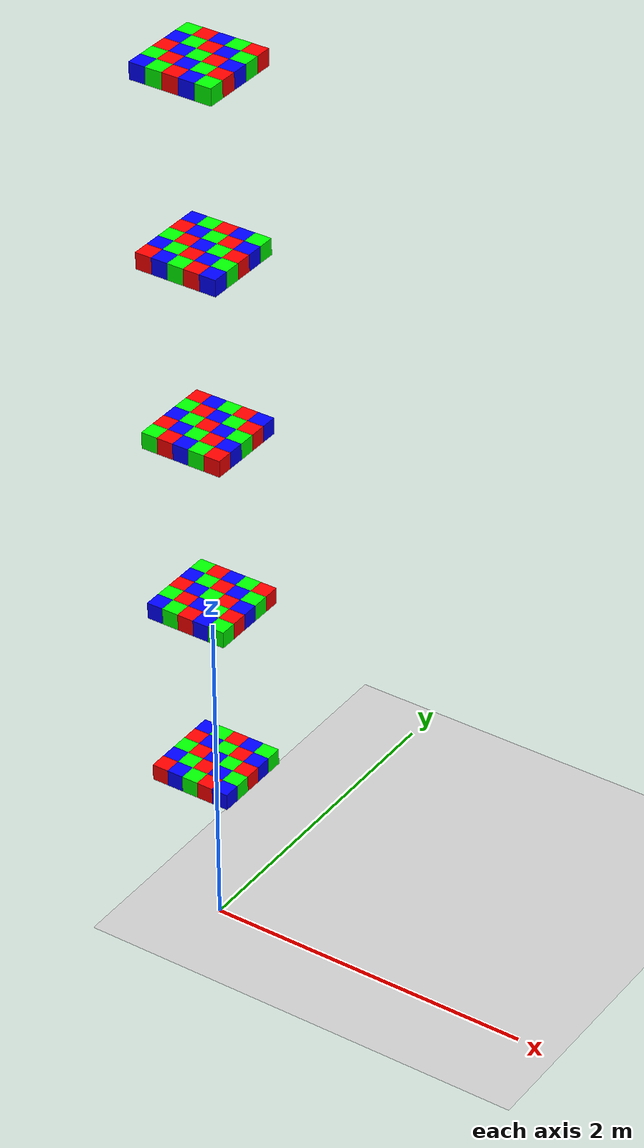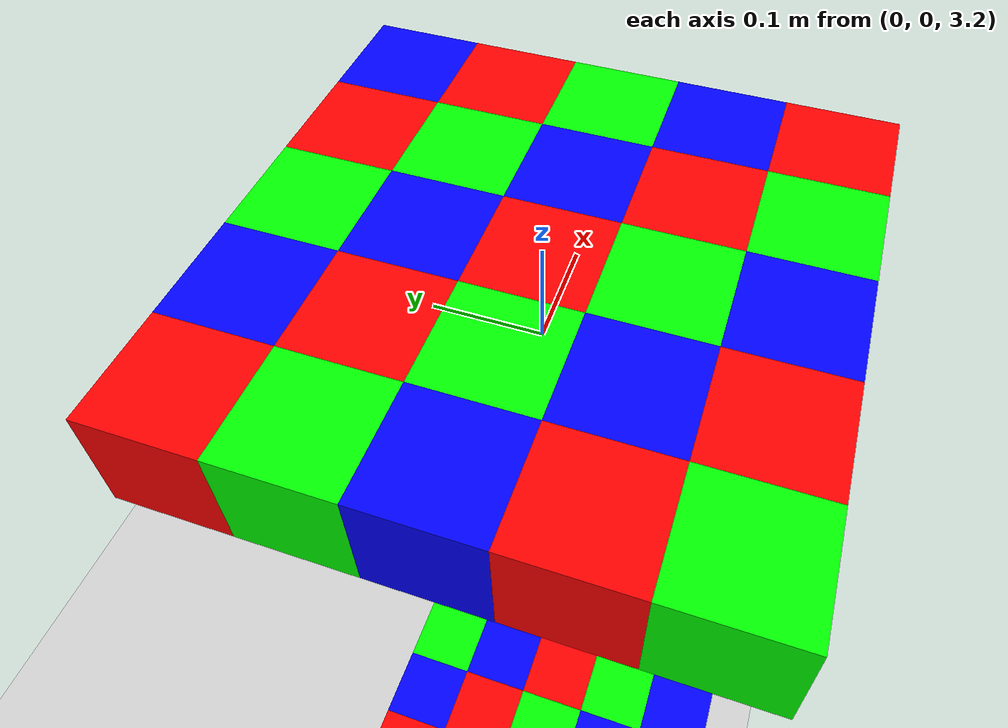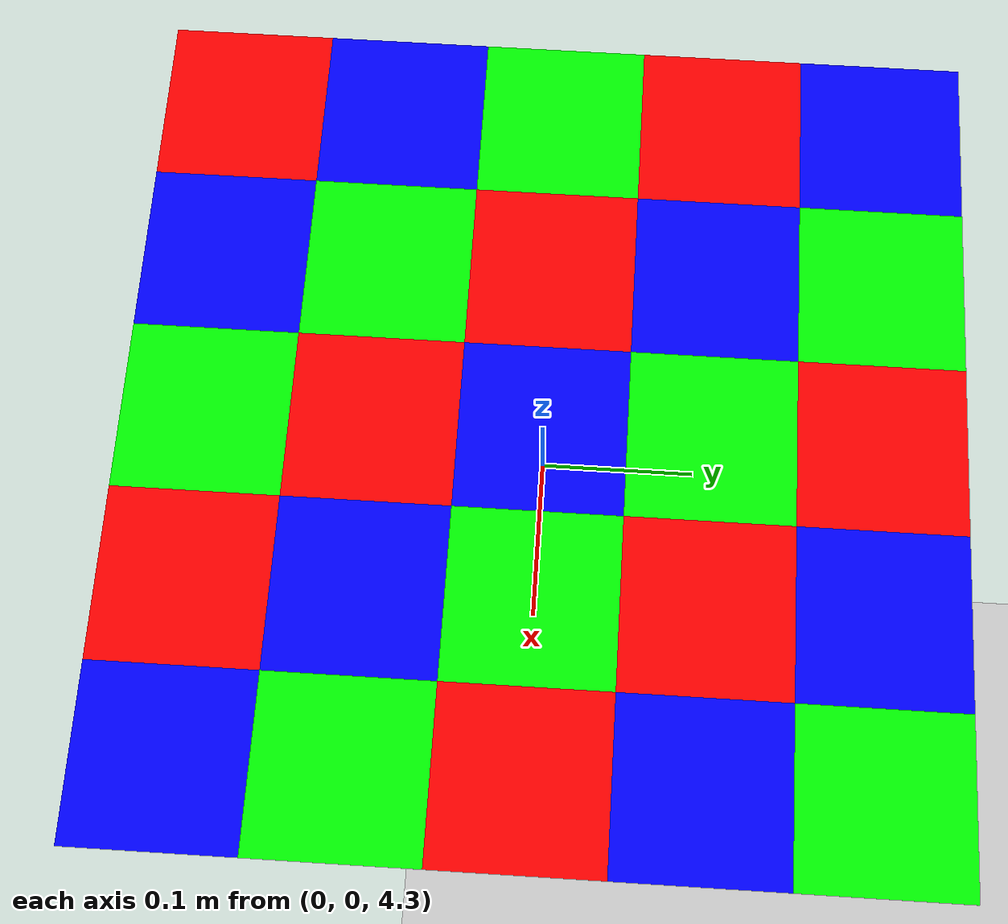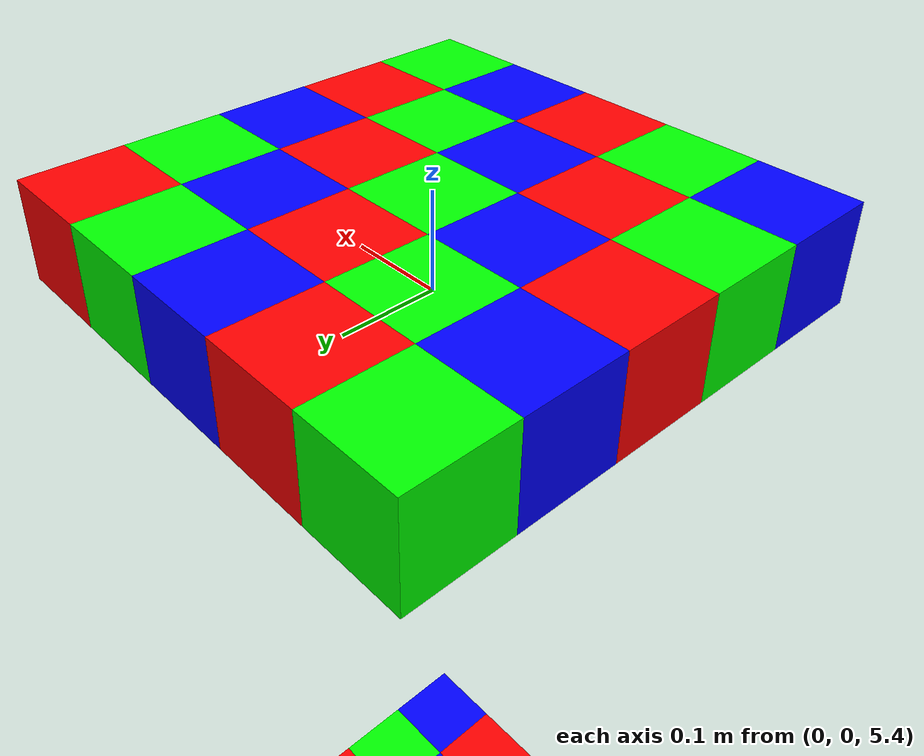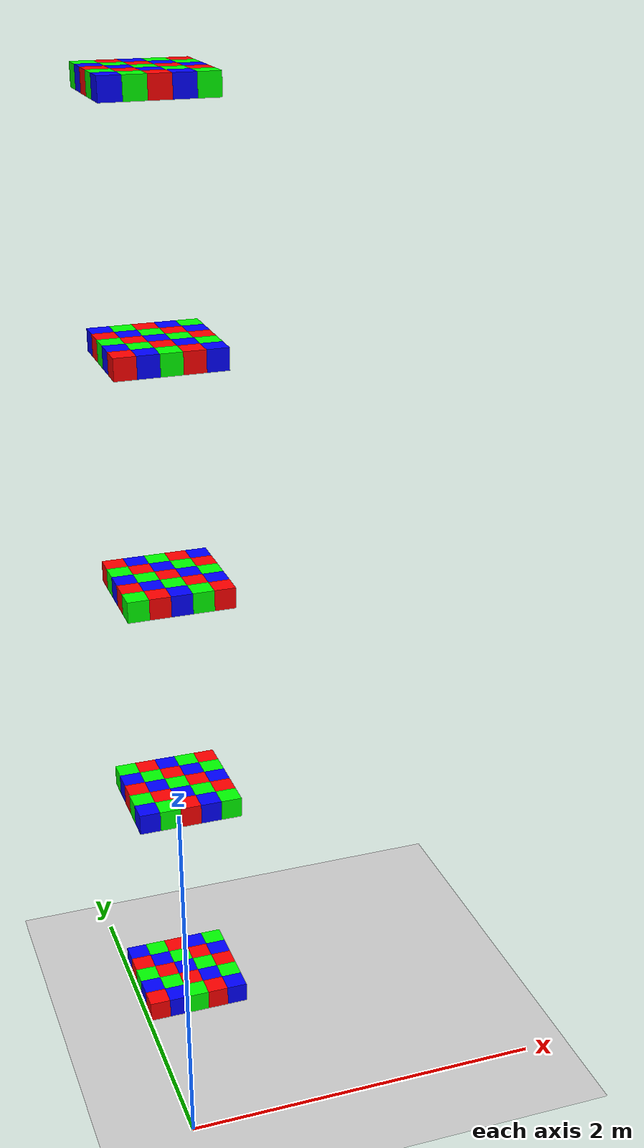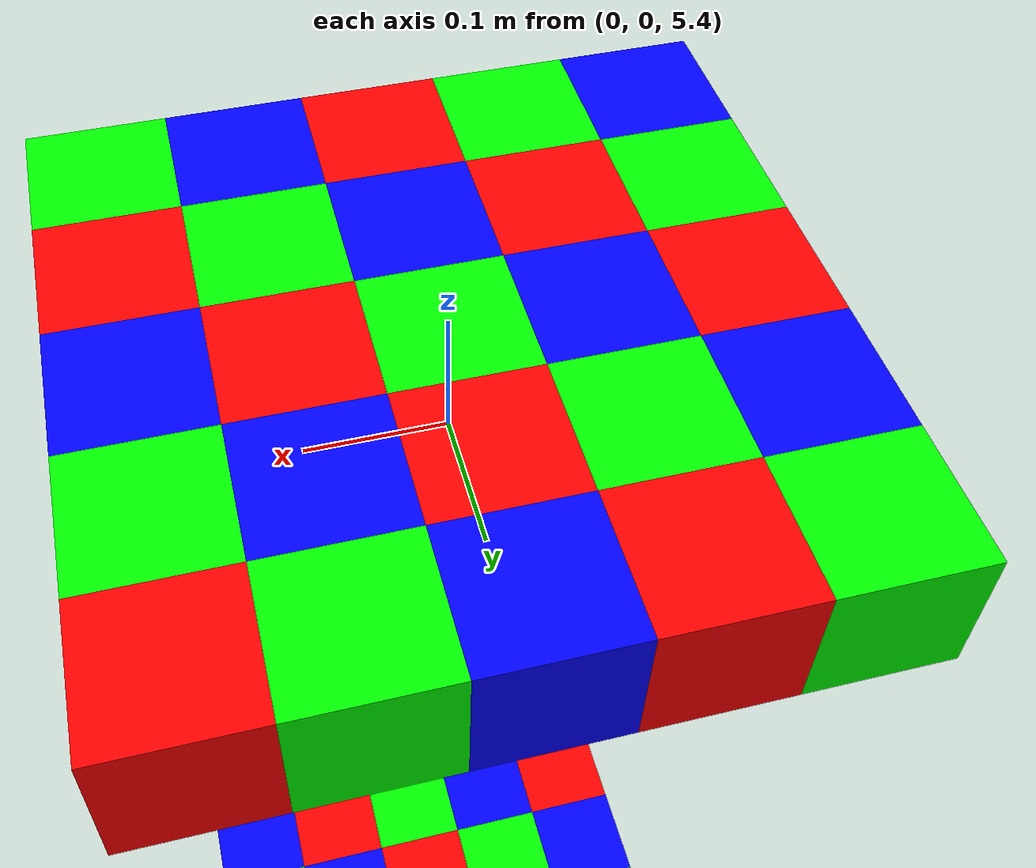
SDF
<?xml version="1.0" ?>
<!--
  A 5x5 grid of 0.1m x 0.1m x 0.1m boxes stacked 5 layers high (125 boxes total).
  Z spacing of 1m between the lowest stack and the ground plane, and 1m spacing between each layer.
-->
<sdf version="1.12">
  <world name="boxes_stack">
    <physics name="1ms" type="ignored">
      <max_step_size>0.001</max_step_size>
      <real_time_factor>1.0</real_time_factor>
    </physics>
    <plugin
      filename="gz-sim-physics-system"
      name="gz::sim::systems::Physics">
    </plugin>
    <plugin
      filename="gz-sim-user-commands-system"
      name="gz::sim::systems::UserCommands">
    </plugin>
    <plugin
      filename="gz-sim-scene-broadcaster-system"
      name="gz::sim::systems::SceneBroadcaster">
    </plugin>

    <scene>
      <ambient>1.0 1.0 1.0</ambient>
      <background>0.8 0.8 0.8</background>
    </scene>

    <light type="directional" name="sun">
      <cast_shadows>true</cast_shadows>
      <pose>0 0 10 0 0 0</pose>
      <diffuse>0.8 0.8 0.8 1</diffuse>
      <specular>0.8 0.8 0.8 1</specular>
      <attenuation>
        <range>1000</range>
        <constant>0.9</constant>
        <linear>0.01</linear>
        <quadratic>0.001</quadratic>
      </attenuation>
      <direction>-0.5 0.1 -0.9</direction>
    </light>

    <model name="ground_plane">
      <static>true</static>
      <link name="link">
        <collision name="collision">
          <geometry>
            <plane>
              <normal>0 0 1</normal>
            </plane>
          </geometry>
        </collision>
        <visual name="visual">
          <geometry>
            <plane>
              <normal>0 0 1</normal>
              <size>100 100</size>
            </plane>
          </geometry>
          <material>
            <ambient>0.8 0.8 0.8 1</ambient>
            <diffuse>0.8 0.8 0.8 1</diffuse>
            <specular>0.8 0.8 0.8 1</specular>
          </material>
        </visual>
      </link>
    </model>

    <model name="box_0">
      <pose>-0.2 -0.2 1.05 0 0 0</pose>
      <link name="box_link">
        <inertial auto="true" />
        <collision name="box_collision">
          <density>1000</density>
          <geometry>
            <box>
              <size>0.1 0.1 0.1</size>
            </box>
          </geometry>
        </collision>
        <visual name="box_visual">
          <geometry>
            <box>
              <size>0.1 0.1 0.1</size>
            </box>
          </geometry>
          <material>
            <ambient>1 0 0 1</ambient>
            <diffuse>1 0 0 1</diffuse>
            <specular>1 1 1 1</specular>
            <pbr>
              <metal>
                <metalness>0.1</metalness>
                <roughness>0.3</roughness>
              </metal>
            </pbr>
          </material>
        </visual>
      </link>
    </model>
    <model name="box_1">
      <pose>-0.2 -0.1 1.05 0 0 0</pose>
      <link name="box_link">
        <inertial auto="true" />
        <collision name="box_collision">
          <density>1000</density>
          <geometry>
            <box>
              <size>0.1 0.1 0.1</size>
            </box>
          </geometry>
        </collision>
        <visual name="box_visual">
          <geometry>
            <box>
              <size>0.1 0.1 0.1</size>
            </box>
          </geometry>
          <material>
            <ambient>0 0 1 1</ambient>
            <diffuse>0 0 1 1</diffuse>
            <specular>1 1 1 1</specular>
            <pbr>
              <metal>
                <metalness>0.1</metalness>
                <roughness>0.3</roughness>
              </metal>
            </pbr>
          </material>
        </visual>
      </link>
    </model>
    <model name="box_2">
      <pose>-0.2 0 1.05 0 0 0</pose>
      <link name="box_link">
        <inertial auto="true" />
        <collision name="box_collision">
          <density>1000</density>
          <geometry>
            <box>
              <size>0.1 0.1 0.1</size>
            </box>
          </geometry>
        </collision>
        <visual name="box_visual">
          <geometry>
            <box>
              <size>0.1 0.1 0.1</size>
            </box>
          </geometry>
          <material>
            <ambient>0 1 0 1</ambient>
            <diffuse>0 1 0 1</diffuse>
            <specular>1 1 1 1</specular>
            <pbr>
              <metal>
                <metalness>0.1</metalness>
                <roughness>0.3</roughness>
              </metal>
            </pbr>
          </material>
        </visual>
      </link>
    </model>
    <model name="box_3">
      <pose>-0.2 0.1 1.05 0 0 0</pose>
      <link name="box_link">
        <inertial auto="true" />
        <collision name="box_collision">
          <density>1000</density>
          <geometry>
            <box>
              <size>0.1 0.1 0.1</size>
            </box>
          </geometry>
        </collision>
        <visual name="box_visual">
          <geometry>
            <box>
              <size>0.1 0.1 0.1</size>
            </box>
          </geometry>
          <material>
            <ambient>1 0 0 1</ambient>
            <diffuse>1 0 0 1</diffuse>
            <specular>1 1 1 1</specular>
            <pbr>
              <metal>
                <metalness>0.1</metalness>
                <roughness>0.3</roughness>
              </metal>
            </pbr>
          </material>
        </visual>
      </link>
    </model>
    <model name="box_4">
      <pose>-0.2 0.2 1.05 0 0 0</pose>
      <link name="box_link">
        <inertial auto="true" />
        <collision name="box_collision">
          <density>1000</density>
          <geometry>
            <box>
              <size>0.1 0.1 0.1</size>
            </box>
          </geometry>
        </collision>
        <visual name="box_visual">
          <geometry>
            <box>
              <size>0.1 0.1 0.1</size>
            </box>
          </geometry>
          <material>
            <ambient>0 0 1 1</ambient>
            <diffuse>0 0 1 1</diffuse>
            <specular>1 1 1 1</specular>
            <pbr>
              <metal>
                <metalness>0.1</metalness>
                <roughness>0.3</roughness>
              </metal>
            </pbr>
          </material>
        </visual>
      </link>
    </model>
    <model name="box_5">
      <pose>-0.1 -0.2 1.05 0 0 0</pose>
      <link name="box_link">
        <inertial auto="true" />
        <collision name="box_collision">
          <density>1000</density>
          <geometry>
            <box>
              <size>0.1 0.1 0.1</size>
            </box>
          </geometry>
        </collision>
        <visual name="box_visual">
          <geometry>
            <box>
              <size>0.1 0.1 0.1</size>
            </box>
          </geometry>
          <material>
            <ambient>0 0 1 1</ambient>
            <diffuse>0 0 1 1</diffuse>
            <specular>1 1 1 1</specular>
            <pbr>
              <metal>
                <metalness>0.1</metalness>
                <roughness>0.3</roughness>
              </metal>
            </pbr>
          </material>
        </visual>
      </link>
    </model>
    <model name="box_6">
      <pose>-0.1 -0.1 1.05 0 0 0</pose>
      <link name="box_link">
        <inertial auto="true" />
        <collision name="box_collision">
          <density>1000</density>
          <geometry>
            <box>
              <size>0.1 0.1 0.1</size>
            </box>
          </geometry>
        </collision>
        <visual name="box_visual">
          <geometry>
            <box>
              <size>0.1 0.1 0.1</size>
            </box>
          </geometry>
          <material>
            <ambient>0 1 0 1</ambient>
            <diffuse>0 1 0 1</diffuse>
            <specular>1 1 1 1</specular>
            <pbr>
              <metal>
                <metalness>0.1</metalness>
                <roughness>0.3</roughness>
              </metal>
            </pbr>
          </material>
        </visual>
      </link>
    </model>
    <model name="box_7">
      <pose>-0.1 0 1.05 0 0 0</pose>
      <link name="box_link">
        <inertial auto="true" />
        <collision name="box_collision">
          <density>1000</density>
          <geometry>
            <box>
              <size>0.1 0.1 0.1</size>
            </box>
          </geometry>
        </collision>
        <visual name="box_visual">
          <geometry>
            <box>
              <size>0.1 0.1 0.1</size>
            </box>
          </geometry>
          <material>
            <ambient>1 0 0 1</ambient>
            <diffuse>1 0 0 1</diffuse>
            <specular>1 1 1 1</specular>
            <pbr>
              <metal>
                <metalness>0.1</metalness>
                <roughness>0.3</roughness>
              </metal>
            </pbr>
          </material>
        </visual>
      </link>
    </model>
    <model name="box_8">
      <pose>-0.1 0.1 1.05 0 0 0</pose>
      <link name="box_link">
        <inertial auto="true" />
        <collision name="box_collision">
          <density>1000</density>
          <geometry>
            <box>
              <size>0.1 0.1 0.1</size>
            </box>
          </geometry>
        </collision>
        <visual name="box_visual">
          <geometry>
            <box>
              <size>0.1 0.1 0.1</size>
            </box>
          </geometry>
          <material>
            <ambient>0 0 1 1</ambient>
            <diffuse>0 0 1 1</diffuse>
            <specular>1 1 1 1</specular>
            <pbr>
              <metal>
                <metalness>0.1</metalness>
                <roughness>0.3</roughness>
              </metal>
            </pbr>
          </material>
        </visual>
      </link>
    </model>
    <model name="box_9">
      <pose>-0.1 0.2 1.05 0 0 0</pose>
      <link name="box_link">
        <inertial auto="true" />
        <collision name="box_collision">
          <density>1000</density>
          <geometry>
            <box>
              <size>0.1 0.1 0.1</size>
            </box>
          </geometry>
        </collision>
        <visual name="box_visual">
          <geometry>
            <box>
              <size>0.1 0.1 0.1</size>
            </box>
          </geometry>
          <material>
            <ambient>0 1 0 1</ambient>
            <diffuse>0 1 0 1</diffuse>
            <specular>1 1 1 1</specular>
            <pbr>
              <metal>
                <metalness>0.1</metalness>
                <roughness>0.3</roughness>
              </metal>
            </pbr>
          </material>
        </visual>
      </link>
    </model>
    <model name="box_10">
      <pose>0 -0.2 1.05 0 0 0</pose>
      <link name="box_link">
        <inertial auto="true" />
        <collision name="box_collision">
          <density>1000</density>
          <geometry>
            <box>
              <size>0.1 0.1 0.1</size>
            </box>
          </geometry>
        </collision>
        <visual name="box_visual">
          <geometry>
            <box>
              <size>0.1 0.1 0.1</size>
            </box>
          </geometry>
          <material>
            <ambient>0 1 0 1</ambient>
            <diffuse>0 1 0 1</diffuse>
            <specular>1 1 1 1</specular>
            <pbr>
              <metal>
                <metalness>0.1</metalness>
                <roughness>0.3</roughness>
              </metal>
            </pbr>
          </material>
        </visual>
      </link>
    </model>
    <model name="box_11">
      <pose>0 -0.1 1.05 0 0 0</pose>
      <link name="box_link">
        <inertial auto="true" />
        <collision name="box_collision">
          <density>1000</density>
          <geometry>
            <box>
              <size>0.1 0.1 0.1</size>
            </box>
          </geometry>
        </collision>
        <visual name="box_visual">
          <geometry>
            <box>
              <size>0.1 0.1 0.1</size>
            </box>
          </geometry>
          <material>
            <ambient>1 0 0 1</ambient>
            <diffuse>1 0 0 1</diffuse>
            <specular>1 1 1 1</specular>
            <pbr>
              <metal>
                <metalness>0.1</metalness>
                <roughness>0.3</roughness>
              </metal>
            </pbr>
          </material>
        </visual>
      </link>
    </model>
    <model name="box_12">
      <pose>0 0 1.05 0 0 0</pose>
      <link name="box_link">
        <inertial auto="true" />
        <collision name="box_collision">
          <density>1000</density>
          <geometry>
            <box>
              <size>0.1 0.1 0.1</size>
            </box>
          </geometry>
        </collision>
        <visual name="box_visual">
          <geometry>
            <box>
              <size>0.1 0.1 0.1</size>
            </box>
          </geometry>
          <material>
            <ambient>0 0 1 1</ambient>
            <diffuse>0 0 1 1</diffuse>
            <specular>1 1 1 1</specular>
            <pbr>
              <metal>
                <metalness>0.1</metalness>
                <roughness>0.3</roughness>
              </metal>
            </pbr>
          </material>
        </visual>
      </link>
    </model>
    <model name="box_13">
      <pose>0 0.1 1.05 0 0 0</pose>
      <link name="box_link">
        <inertial auto="true" />
        <collision name="box_collision">
          <density>1000</density>
          <geometry>
            <box>
              <size>0.1 0.1 0.1</size>
            </box>
          </geometry>
        </collision>
        <visual name="box_visual">
          <geometry>
            <box>
              <size>0.1 0.1 0.1</size>
            </box>
          </geometry>
          <material>
            <ambient>0 1 0 1</ambient>
            <diffuse>0 1 0 1</diffuse>
            <specular>1 1 1 1</specular>
            <pbr>
              <metal>
                <metalness>0.1</metalness>
                <roughness>0.3</roughness>
              </metal>
            </pbr>
          </material>
        </visual>
      </link>
    </model>
    <model name="box_14">
      <pose>0 0.2 1.05 0 0 0</pose>
      <link name="box_link">
        <inertial auto="true" />
        <collision name="box_collision">
          <density>1000</density>
          <geometry>
            <box>
              <size>0.1 0.1 0.1</size>
            </box>
          </geometry>
        </collision>
        <visual name="box_visual">
          <geometry>
            <box>
              <size>0.1 0.1 0.1</size>
            </box>
          </geometry>
          <material>
            <ambient>1 0 0 1</ambient>
            <diffuse>1 0 0 1</diffuse>
            <specular>1 1 1 1</specular>
            <pbr>
              <metal>
                <metalness>0.1</metalness>
                <roughness>0.3</roughness>
              </metal>
            </pbr>
          </material>
        </visual>
      </link>
    </model>
    <model name="box_15">
      <pose>0.1 -0.2 1.05 0 0 0</pose>
      <link name="box_link">
        <inertial auto="true" />
        <collision name="box_collision">
          <density>1000</density>
          <geometry>
            <box>
              <size>0.1 0.1 0.1</size>
            </box>
          </geometry>
        </collision>
        <visual name="box_visual">
          <geometry>
            <box>
              <size>0.1 0.1 0.1</size>
            </box>
          </geometry>
          <material>
            <ambient>1 0 0 1</ambient>
            <diffuse>1 0 0 1</diffuse>
            <specular>1 1 1 1</specular>
            <pbr>
              <metal>
                <metalness>0.1</metalness>
                <roughness>0.3</roughness>
              </metal>
            </pbr>
          </material>
        </visual>
      </link>
    </model>
    <model name="box_16">
      <pose>0.1 -0.1 1.05 0 0 0</pose>
      <link name="box_link">
        <inertial auto="true" />
        <collision name="box_collision">
          <density>1000</density>
          <geometry>
            <box>
              <size>0.1 0.1 0.1</size>
            </box>
          </geometry>
        </collision>
        <visual name="box_visual">
          <geometry>
            <box>
              <size>0.1 0.1 0.1</size>
            </box>
          </geometry>
          <material>
            <ambient>0 0 1 1</ambient>
            <diffuse>0 0 1 1</diffuse>
            <specular>1 1 1 1</specular>
            <pbr>
              <metal>
                <metalness>0.1</metalness>
                <roughness>0.3</roughness>
              </metal>
            </pbr>
          </material>
        </visual>
      </link>
    </model>
    <model name="box_17">
      <pose>0.1 0 1.05 0 0 0</pose>
      <link name="box_link">
        <inertial auto="true" />
        <collision name="box_collision">
          <density>1000</density>
          <geometry>
            <box>
              <size>0.1 0.1 0.1</size>
            </box>
          </geometry>
        </collision>
        <visual name="box_visual">
          <geometry>
            <box>
              <size>0.1 0.1 0.1</size>
            </box>
          </geometry>
          <material>
            <ambient>0 1 0 1</ambient>
            <diffuse>0 1 0 1</diffuse>
            <specular>1 1 1 1</specular>
            <pbr>
              <metal>
                <metalness>0.1</metalness>
                <roughness>0.3</roughness>
              </metal>
            </pbr>
          </material>
        </visual>
      </link>
    </model>
    <model name="box_18">
      <pose>0.1 0.1 1.05 0 0 0</pose>
      <link name="box_link">
        <inertial auto="true" />
        <collision name="box_collision">
          <density>1000</density>
          <geometry>
            <box>
              <size>0.1 0.1 0.1</size>
            </box>
          </geometry>
        </collision>
        <visual name="box_visual">
          <geometry>
            <box>
              <size>0.1 0.1 0.1</size>
            </box>
          </geometry>
          <material>
            <ambient>1 0 0 1</ambient>
            <diffuse>1 0 0 1</diffuse>
            <specular>1 1 1 1</specular>
            <pbr>
              <metal>
                <metalness>0.1</metalness>
                <roughness>0.3</roughness>
              </metal>
            </pbr>
          </material>
        </visual>
      </link>
    </model>
    <model name="box_19">
      <pose>0.1 0.2 1.05 0 0 0</pose>
      <link name="box_link">
        <inertial auto="true" />
        <collision name="box_collision">
          <density>1000</density>
          <geometry>
            <box>
              <size>0.1 0.1 0.1</size>
            </box>
          </geometry>
        </collision>
        <visual name="box_visual">
          <geometry>
            <box>
              <size>0.1 0.1 0.1</size>
            </box>
          </geometry>
          <material>
            <ambient>0 0 1 1</ambient>
            <diffuse>0 0 1 1</diffuse>
            <specular>1 1 1 1</specular>
            <pbr>
              <metal>
                <metalness>0.1</metalness>
                <roughness>0.3</roughness>
              </metal>
            </pbr>
          </material>
        </visual>
      </link>
    </model>
    <model name="box_20">
      <pose>0.2 -0.2 1.05 0 0 0</pose>
      <link name="box_link">
        <inertial auto="true" />
        <collision name="box_collision">
          <density>1000</density>
          <geometry>
            <box>
              <size>0.1 0.1 0.1</size>
            </box>
          </geometry>
        </collision>
        <visual name="box_visual">
          <geometry>
            <box>
              <size>0.1 0.1 0.1</size>
            </box>
          </geometry>
          <material>
            <ambient>0 0 1 1</ambient>
            <diffuse>0 0 1 1</diffuse>
            <specular>1 1 1 1</specular>
            <pbr>
              <metal>
                <metalness>0.1</metalness>
                <roughness>0.3</roughness>
              </metal>
            </pbr>
          </material>
        </visual>
      </link>
    </model>
    <model name="box_21">
      <pose>0.2 -0.1 1.05 0 0 0</pose>
      <link name="box_link">
        <inertial auto="true" />
        <collision name="box_collision">
          <density>1000</density>
          <geometry>
            <box>
              <size>0.1 0.1 0.1</size>
            </box>
          </geometry>
        </collision>
        <visual name="box_visual">
          <geometry>
            <box>
              <size>0.1 0.1 0.1</size>
            </box>
          </geometry>
          <material>
            <ambient>0 1 0 1</ambient>
            <diffuse>0 1 0 1</diffuse>
            <specular>1 1 1 1</specular>
            <pbr>
              <metal>
                <metalness>0.1</metalness>
                <roughness>0.3</roughness>
              </metal>
            </pbr>
          </material>
        </visual>
      </link>
    </model>
    <model name="box_22">
      <pose>0.2 0 1.05 0 0 0</pose>
      <link name="box_link">
        <inertial auto="true" />
        <collision name="box_collision">
          <density>1000</density>
          <geometry>
            <box>
              <size>0.1 0.1 0.1</size>
            </box>
          </geometry>
        </collision>
        <visual name="box_visual">
          <geometry>
            <box>
              <size>0.1 0.1 0.1</size>
            </box>
          </geometry>
          <material>
            <ambient>1 0 0 1</ambient>
            <diffuse>1 0 0 1</diffuse>
            <specular>1 1 1 1</specular>
            <pbr>
              <metal>
                <metalness>0.1</metalness>
                <roughness>0.3</roughness>
              </metal>
            </pbr>
          </material>
        </visual>
      </link>
    </model>
    <model name="box_23">
      <pose>0.2 0.1 1.05 0 0 0</pose>
      <link name="box_link">
        <inertial auto="true" />
        <collision name="box_collision">
          <density>1000</density>
          <geometry>
            <box>
              <size>0.1 0.1 0.1</size>
            </box>
          </geometry>
        </collision>
        <visual name="box_visual">
          <geometry>
            <box>
              <size>0.1 0.1 0.1</size>
            </box>
          </geometry>
          <material>
            <ambient>0 0 1 1</ambient>
            <diffuse>0 0 1 1</diffuse>
            <specular>1 1 1 1</specular>
            <pbr>
              <metal>
                <metalness>0.1</metalness>
                <roughness>0.3</roughness>
              </metal>
            </pbr>
          </material>
        </visual>
      </link>
    </model>
    <model name="box_24">
      <pose>0.2 0.2 1.05 0 0 0</pose>
      <link name="box_link">
        <inertial auto="true" />
        <collision name="box_collision">
          <density>1000</density>
          <geometry>
            <box>
              <size>0.1 0.1 0.1</size>
            </box>
          </geometry>
        </collision>
        <visual name="box_visual">
          <geometry>
            <box>
              <size>0.1 0.1 0.1</size>
            </box>
          </geometry>
          <material>
            <ambient>0 1 0 1</ambient>
            <diffuse>0 1 0 1</diffuse>
            <specular>1 1 1 1</specular>
            <pbr>
              <metal>
                <metalness>0.1</metalness>
                <roughness>0.3</roughness>
              </metal>
            </pbr>
          </material>
        </visual>
      </link>
    </model>
    <model name="box_25">
      <pose>-0.2 -0.2 2.15 0 0 0</pose>
      <link name="box_link">
        <inertial auto="true" />
        <collision name="box_collision">
          <density>1000</density>
          <geometry>
            <box>
              <size>0.1 0.1 0.1</size>
            </box>
          </geometry>
        </collision>
        <visual name="box_visual">
          <geometry>
            <box>
              <size>0.1 0.1 0.1</size>
            </box>
          </geometry>
          <material>
            <ambient>0 0 1 1</ambient>
            <diffuse>0 0 1 1</diffuse>
            <specular>1 1 1 1</specular>
            <pbr>
              <metal>
                <metalness>0.1</metalness>
                <roughness>0.3</roughness>
              </metal>
            </pbr>
          </material>
        </visual>
      </link>
    </model>
    <model name="box_26">
      <pose>-0.2 -0.1 2.15 0 0 0</pose>
      <link name="box_link">
        <inertial auto="true" />
        <collision name="box_collision">
          <density>1000</density>
          <geometry>
            <box>
              <size>0.1 0.1 0.1</size>
            </box>
          </geometry>
        </collision>
        <visual name="box_visual">
          <geometry>
            <box>
              <size>0.1 0.1 0.1</size>
            </box>
          </geometry>
          <material>
            <ambient>0 1 0 1</ambient>
            <diffuse>0 1 0 1</diffuse>
            <specular>1 1 1 1</specular>
            <pbr>
              <metal>
                <metalness>0.1</metalness>
                <roughness>0.3</roughness>
              </metal>
            </pbr>
          </material>
        </visual>
      </link>
    </model>
    <model name="box_27">
      <pose>-0.2 0 2.15 0 0 0</pose>
      <link name="box_link">
        <inertial auto="true" />
        <collision name="box_collision">
          <density>1000</density>
          <geometry>
            <box>
              <size>0.1 0.1 0.1</size>
            </box>
          </geometry>
        </collision>
        <visual name="box_visual">
          <geometry>
            <box>
              <size>0.1 0.1 0.1</size>
            </box>
          </geometry>
          <material>
            <ambient>1 0 0 1</ambient>
            <diffuse>1 0 0 1</diffuse>
            <specular>1 1 1 1</specular>
            <pbr>
              <metal>
                <metalness>0.1</metalness>
                <roughness>0.3</roughness>
              </metal>
            </pbr>
          </material>
        </visual>
      </link>
    </model>
    <model name="box_28">
      <pose>-0.2 0.1 2.15 0 0 0</pose>
      <link name="box_link">
        <inertial auto="true" />
        <collision name="box_collision">
          <density>1000</density>
          <geometry>
            <box>
              <size>0.1 0.1 0.1</size>
            </box>
          </geometry>
        </collision>
        <visual name="box_visual">
          <geometry>
            <box>
              <size>0.1 0.1 0.1</size>
            </box>
          </geometry>
          <material>
            <ambient>0 0 1 1</ambient>
            <diffuse>0 0 1 1</diffuse>
            <specular>1 1 1 1</specular>
            <pbr>
              <metal>
                <metalness>0.1</metalness>
                <roughness>0.3</roughness>
              </metal>
            </pbr>
          </material>
        </visual>
      </link>
    </model>
    <model name="box_29">
      <pose>-0.2 0.2 2.15 0 0 0</pose>
      <link name="box_link">
        <inertial auto="true" />
        <collision name="box_collision">
          <density>1000</density>
          <geometry>
            <box>
              <size>0.1 0.1 0.1</size>
            </box>
          </geometry>
        </collision>
        <visual name="box_visual">
          <geometry>
            <box>
              <size>0.1 0.1 0.1</size>
            </box>
          </geometry>
          <material>
            <ambient>0 1 0 1</ambient>
            <diffuse>0 1 0 1</diffuse>
            <specular>1 1 1 1</specular>
            <pbr>
              <metal>
                <metalness>0.1</metalness>
                <roughness>0.3</roughness>
              </metal>
            </pbr>
          </material>
        </visual>
      </link>
    </model>
    <model name="box_30">
      <pose>-0.1 -0.2 2.15 0 0 0</pose>
      <link name="box_link">
        <inertial auto="true" />
        <collision name="box_collision">
          <density>1000</density>
          <geometry>
            <box>
              <size>0.1 0.1 0.1</size>
            </box>
          </geometry>
        </collision>
        <visual name="box_visual">
          <geometry>
            <box>
              <size>0.1 0.1 0.1</size>
            </box>
          </geometry>
          <material>
            <ambient>0 1 0 1</ambient>
            <diffuse>0 1 0 1</diffuse>
            <specular>1 1 1 1</specular>
            <pbr>
              <metal>
                <metalness>0.1</metalness>
                <roughness>0.3</roughness>
              </metal>
            </pbr>
          </material>
        </visual>
      </link>
    </model>
    <model name="box_31">
      <pose>-0.1 -0.1 2.15 0 0 0</pose>
      <link name="box_link">
        <inertial auto="true" />
        <collision name="box_collision">
          <density>1000</density>
          <geometry>
            <box>
              <size>0.1 0.1 0.1</size>
            </box>
          </geometry>
        </collision>
        <visual name="box_visual">
          <geometry>
            <box>
              <size>0.1 0.1 0.1</size>
            </box>
          </geometry>
          <material>
            <ambient>1 0 0 1</ambient>
            <diffuse>1 0 0 1</diffuse>
            <specular>1 1 1 1</specular>
            <pbr>
              <metal>
                <metalness>0.1</metalness>
                <roughness>0.3</roughness>
              </metal>
            </pbr>
          </material>
        </visual>
      </link>
    </model>
    <model name="box_32">
      <pose>-0.1 0 2.15 0 0 0</pose>
      <link name="box_link">
        <inertial auto="true" />
        <collision name="box_collision">
          <density>1000</density>
          <geometry>
            <box>
              <size>0.1 0.1 0.1</size>
            </box>
          </geometry>
        </collision>
        <visual name="box_visual">
          <geometry>
            <box>
              <size>0.1 0.1 0.1</size>
            </box>
          </geometry>
          <material>
            <ambient>0 0 1 1</ambient>
            <diffuse>0 0 1 1</diffuse>
            <specular>1 1 1 1</specular>
            <pbr>
              <metal>
                <metalness>0.1</metalness>
                <roughness>0.3</roughness>
              </metal>
            </pbr>
          </material>
        </visual>
      </link>
    </model>
    <model name="box_33">
      <pose>-0.1 0.1 2.15 0 0 0</pose>
      <link name="box_link">
        <inertial auto="true" />
        <collision name="box_collision">
          <density>1000</density>
          <geometry>
            <box>
              <size>0.1 0.1 0.1</size>
            </box>
          </geometry>
        </collision>
        <visual name="box_visual">
          <geometry>
            <box>
              <size>0.1 0.1 0.1</size>
            </box>
          </geometry>
          <material>
            <ambient>0 1 0 1</ambient>
            <diffuse>0 1 0 1</diffuse>
            <specular>1 1 1 1</specular>
            <pbr>
              <metal>
                <metalness>0.1</metalness>
                <roughness>0.3</roughness>
              </metal>
            </pbr>
          </material>
        </visual>
      </link>
    </model>
    <model name="box_34">
      <pose>-0.1 0.2 2.15 0 0 0</pose>
      <link name="box_link">
        <inertial auto="true" />
        <collision name="box_collision">
          <density>1000</density>
          <geometry>
            <box>
              <size>0.1 0.1 0.1</size>
            </box>
          </geometry>
        </collision>
        <visual name="box_visual">
          <geometry>
            <box>
              <size>0.1 0.1 0.1</size>
            </box>
          </geometry>
          <material>
            <ambient>1 0 0 1</ambient>
            <diffuse>1 0 0 1</diffuse>
            <specular>1 1 1 1</specular>
            <pbr>
              <metal>
                <metalness>0.1</metalness>
                <roughness>0.3</roughness>
              </metal>
            </pbr>
          </material>
        </visual>
      </link>
    </model>
    <model name="box_35">
      <pose>0 -0.2 2.15 0 0 0</pose>
      <link name="box_link">
        <inertial auto="true" />
        <collision name="box_collision">
          <density>1000</density>
          <geometry>
            <box>
              <size>0.1 0.1 0.1</size>
            </box>
          </geometry>
        </collision>
        <visual name="box_visual">
          <geometry>
            <box>
              <size>0.1 0.1 0.1</size>
            </box>
          </geometry>
          <material>
            <ambient>1 0 0 1</ambient>
            <diffuse>1 0 0 1</diffuse>
            <specular>1 1 1 1</specular>
            <pbr>
              <metal>
                <metalness>0.1</metalness>
                <roughness>0.3</roughness>
              </metal>
            </pbr>
          </material>
        </visual>
      </link>
    </model>
    <model name="box_36">
      <pose>0 -0.1 2.15 0 0 0</pose>
      <link name="box_link">
        <inertial auto="true" />
        <collision name="box_collision">
          <density>1000</density>
          <geometry>
            <box>
              <size>0.1 0.1 0.1</size>
            </box>
          </geometry>
        </collision>
        <visual name="box_visual">
          <geometry>
            <box>
              <size>0.1 0.1 0.1</size>
            </box>
          </geometry>
          <material>
            <ambient>0 0 1 1</ambient>
            <diffuse>0 0 1 1</diffuse>
            <specular>1 1 1 1</specular>
            <pbr>
              <metal>
                <metalness>0.1</metalness>
                <roughness>0.3</roughness>
              </metal>
            </pbr>
          </material>
        </visual>
      </link>
    </model>
    <model name="box_37">
      <pose>0 0 2.15 0 0 0</pose>
      <link name="box_link">
        <inertial auto="true" />
        <collision name="box_collision">
          <density>1000</density>
          <geometry>
            <box>
              <size>0.1 0.1 0.1</size>
            </box>
          </geometry>
        </collision>
        <visual name="box_visual">
          <geometry>
            <box>
              <size>0.1 0.1 0.1</size>
            </box>
          </geometry>
          <material>
            <ambient>0 1 0 1</ambient>
            <diffuse>0 1 0 1</diffuse>
            <specular>1 1 1 1</specular>
            <pbr>
              <metal>
                <metalness>0.1</metalness>
                <roughness>0.3</roughness>
              </metal>
            </pbr>
          </material>
        </visual>
      </link>
    </model>
    <model name="box_38">
      <pose>0 0.1 2.15 0 0 0</pose>
      <link name="box_link">
        <inertial auto="true" />
        <collision name="box_collision">
          <density>1000</density>
          <geometry>
            <box>
              <size>0.1 0.1 0.1</size>
            </box>
          </geometry>
        </collision>
        <visual name="box_visual">
          <geometry>
            <box>
              <size>0.1 0.1 0.1</size>
            </box>
          </geometry>
          <material>
            <ambient>1 0 0 1</ambient>
            <diffuse>1 0 0 1</diffuse>
            <specular>1 1 1 1</specular>
            <pbr>
              <metal>
                <metalness>0.1</metalness>
                <roughness>0.3</roughness>
              </metal>
            </pbr>
          </material>
        </visual>
      </link>
    </model>
    <model name="box_39">
      <pose>0 0.2 2.15 0 0 0</pose>
      <link name="box_link">
        <inertial auto="true" />
        <collision name="box_collision">
          <density>1000</density>
          <geometry>
            <box>
              <size>0.1 0.1 0.1</size>
            </box>
          </geometry>
        </collision>
        <visual name="box_visual">
          <geometry>
            <box>
              <size>0.1 0.1 0.1</size>
            </box>
          </geometry>
          <material>
            <ambient>0 0 1 1</ambient>
            <diffuse>0 0 1 1</diffuse>
            <specular>1 1 1 1</specular>
            <pbr>
              <metal>
                <metalness>0.1</metalness>
                <roughness>0.3</roughness>
              </metal>
            </pbr>
          </material>
        </visual>
      </link>
    </model>
    <model name="box_40">
      <pose>0.1 -0.2 2.15 0 0 0</pose>
      <link name="box_link">
        <inertial auto="true" />
        <collision name="box_collision">
          <density>1000</density>
          <geometry>
            <box>
              <size>0.1 0.1 0.1</size>
            </box>
          </geometry>
        </collision>
        <visual name="box_visual">
          <geometry>
            <box>
              <size>0.1 0.1 0.1</size>
            </box>
          </geometry>
          <material>
            <ambient>0 0 1 1</ambient>
            <diffuse>0 0 1 1</diffuse>
            <specular>1 1 1 1</specular>
            <pbr>
              <metal>
                <metalness>0.1</metalness>
                <roughness>0.3</roughness>
              </metal>
            </pbr>
          </material>
        </visual>
      </link>
    </model>
    <model name="box_41">
      <pose>0.1 -0.1 2.15 0 0 0</pose>
      <link name="box_link">
        <inertial auto="true" />
        <collision name="box_collision">
          <density>1000</density>
          <geometry>
            <box>
              <size>0.1 0.1 0.1</size>
            </box>
          </geometry>
        </collision>
        <visual name="box_visual">
          <geometry>
            <box>
              <size>0.1 0.1 0.1</size>
            </box>
          </geometry>
          <material>
            <ambient>0 1 0 1</ambient>
            <diffuse>0 1 0 1</diffuse>
            <specular>1 1 1 1</specular>
            <pbr>
              <metal>
                <metalness>0.1</metalness>
                <roughness>0.3</roughness>
              </metal>
            </pbr>
          </material>
        </visual>
      </link>
    </model>
    <model name="box_42">
      <pose>0.1 0 2.15 0 0 0</pose>
      <link name="box_link">
        <inertial auto="true" />
        <collision name="box_collision">
          <density>1000</density>
          <geometry>
            <box>
              <size>0.1 0.1 0.1</size>
            </box>
          </geometry>
        </collision>
        <visual name="box_visual">
          <geometry>
            <box>
              <size>0.1 0.1 0.1</size>
            </box>
          </geometry>
          <material>
            <ambient>1 0 0 1</ambient>
            <diffuse>1 0 0 1</diffuse>
            <specular>1 1 1 1</specular>
            <pbr>
              <metal>
                <metalness>0.1</metalness>
                <roughness>0.3</roughness>
              </metal>
            </pbr>
          </material>
        </visual>
      </link>
    </model>
    <model name="box_43">
      <pose>0.1 0.1 2.15 0 0 0</pose>
      <link name="box_link">
        <inertial auto="true" />
        <collision name="box_collision">
          <density>1000</density>
          <geometry>
            <box>
              <size>0.1 0.1 0.1</size>
            </box>
          </geometry>
        </collision>
        <visual name="box_visual">
          <geometry>
            <box>
              <size>0.1 0.1 0.1</size>
            </box>
          </geometry>
          <material>
            <ambient>0 0 1 1</ambient>
            <diffuse>0 0 1 1</diffuse>
            <specular>1 1 1 1</specular>
            <pbr>
              <metal>
                <metalness>0.1</metalness>
                <roughness>0.3</roughness>
              </metal>
            </pbr>
          </material>
        </visual>
      </link>
    </model>
    <model name="box_44">
      <pose>0.1 0.2 2.15 0 0 0</pose>
      <link name="box_link">
        <inertial auto="true" />
        <collision name="box_collision">
          <density>1000</density>
          <geometry>
            <box>
              <size>0.1 0.1 0.1</size>
            </box>
          </geometry>
        </collision>
        <visual name="box_visual">
          <geometry>
            <box>
              <size>0.1 0.1 0.1</size>
            </box>
          </geometry>
          <material>
            <ambient>0 1 0 1</ambient>
            <diffuse>0 1 0 1</diffuse>
            <specular>1 1 1 1</specular>
            <pbr>
              <metal>
                <metalness>0.1</metalness>
                <roughness>0.3</roughness>
              </metal>
            </pbr>
          </material>
        </visual>
      </link>
    </model>
    <model name="box_45">
      <pose>0.2 -0.2 2.15 0 0 0</pose>
      <link name="box_link">
        <inertial auto="true" />
        <collision name="box_collision">
          <density>1000</density>
          <geometry>
            <box>
              <size>0.1 0.1 0.1</size>
            </box>
          </geometry>
        </collision>
        <visual name="box_visual">
          <geometry>
            <box>
              <size>0.1 0.1 0.1</size>
            </box>
          </geometry>
          <material>
            <ambient>0 1 0 1</ambient>
            <diffuse>0 1 0 1</diffuse>
            <specular>1 1 1 1</specular>
            <pbr>
              <metal>
                <metalness>0.1</metalness>
                <roughness>0.3</roughness>
              </metal>
            </pbr>
          </material>
        </visual>
      </link>
    </model>
    <model name="box_46">
      <pose>0.2 -0.1 2.15 0 0 0</pose>
      <link name="box_link">
        <inertial auto="true" />
        <collision name="box_collision">
          <density>1000</density>
          <geometry>
            <box>
              <size>0.1 0.1 0.1</size>
            </box>
          </geometry>
        </collision>
        <visual name="box_visual">
          <geometry>
            <box>
              <size>0.1 0.1 0.1</size>
            </box>
          </geometry>
          <material>
            <ambient>1 0 0 1</ambient>
            <diffuse>1 0 0 1</diffuse>
            <specular>1 1 1 1</specular>
            <pbr>
              <metal>
                <metalness>0.1</metalness>
                <roughness>0.3</roughness>
              </metal>
            </pbr>
          </material>
        </visual>
      </link>
    </model>
    <model name="box_47">
      <pose>0.2 0 2.15 0 0 0</pose>
      <link name="box_link">
        <inertial auto="true" />
        <collision name="box_collision">
          <density>1000</density>
          <geometry>
            <box>
              <size>0.1 0.1 0.1</size>
            </box>
          </geometry>
        </collision>
        <visual name="box_visual">
          <geometry>
            <box>
              <size>0.1 0.1 0.1</size>
            </box>
          </geometry>
          <material>
            <ambient>0 0 1 1</ambient>
            <diffuse>0 0 1 1</diffuse>
            <specular>1 1 1 1</specular>
            <pbr>
              <metal>
                <metalness>0.1</metalness>
                <roughness>0.3</roughness>
              </metal>
            </pbr>
          </material>
        </visual>
      </link>
    </model>
    <model name="box_48">
      <pose>0.2 0.1 2.15 0 0 0</pose>
      <link name="box_link">
        <inertial auto="true" />
        <collision name="box_collision">
          <density>1000</density>
          <geometry>
            <box>
              <size>0.1 0.1 0.1</size>
            </box>
          </geometry>
        </collision>
        <visual name="box_visual">
          <geometry>
            <box>
              <size>0.1 0.1 0.1</size>
            </box>
          </geometry>
          <material>
            <ambient>0 1 0 1</ambient>
            <diffuse>0 1 0 1</diffuse>
            <specular>1 1 1 1</specular>
            <pbr>
              <metal>
                <metalness>0.1</metalness>
                <roughness>0.3</roughness>
              </metal>
            </pbr>
          </material>
        </visual>
      </link>
    </model>
    <model name="box_49">
      <pose>0.2 0.2 2.15 0 0 0</pose>
      <link name="box_link">
        <inertial auto="true" />
        <collision name="box_collision">
          <density>1000</density>
          <geometry>
            <box>
              <size>0.1 0.1 0.1</size>
            </box>
          </geometry>
        </collision>
        <visual name="box_visual">
          <geometry>
            <box>
              <size>0.1 0.1 0.1</size>
            </box>
          </geometry>
          <material>
            <ambient>1 0 0 1</ambient>
            <diffuse>1 0 0 1</diffuse>
            <specular>1 1 1 1</specular>
            <pbr>
              <metal>
                <metalness>0.1</metalness>
                <roughness>0.3</roughness>
              </metal>
            </pbr>
          </material>
        </visual>
      </link>
    </model>
    <model name="box_50">
      <pose>-0.2 -0.2 3.25 0 0 0</pose>
      <link name="box_link">
        <inertial auto="true" />
        <collision name="box_collision">
          <density>1000</density>
          <geometry>
            <box>
              <size>0.1 0.1 0.1</size>
            </box>
          </geometry>
        </collision>
        <visual name="box_visual">
          <geometry>
            <box>
              <size>0.1 0.1 0.1</size>
            </box>
          </geometry>
          <material>
            <ambient>0 1 0 1</ambient>
            <diffuse>0 1 0 1</diffuse>
            <specular>1 1 1 1</specular>
            <pbr>
              <metal>
                <metalness>0.1</metalness>
                <roughness>0.3</roughness>
              </metal>
            </pbr>
          </material>
        </visual>
      </link>
    </model>
    <model name="box_51">
      <pose>-0.2 -0.1 3.25 0 0 0</pose>
      <link name="box_link">
        <inertial auto="true" />
        <collision name="box_collision">
          <density>1000</density>
          <geometry>
            <box>
              <size>0.1 0.1 0.1</size>
            </box>
          </geometry>
        </collision>
        <visual name="box_visual">
          <geometry>
            <box>
              <size>0.1 0.1 0.1</size>
            </box>
          </geometry>
          <material>
            <ambient>1 0 0 1</ambient>
            <diffuse>1 0 0 1</diffuse>
            <specular>1 1 1 1</specular>
            <pbr>
              <metal>
                <metalness>0.1</metalness>
                <roughness>0.3</roughness>
              </metal>
            </pbr>
          </material>
        </visual>
      </link>
    </model>
    <model name="box_52">
      <pose>-0.2 0 3.25 0 0 0</pose>
      <link name="box_link">
        <inertial auto="true" />
        <collision name="box_collision">
          <density>1000</density>
          <geometry>
            <box>
              <size>0.1 0.1 0.1</size>
            </box>
          </geometry>
        </collision>
        <visual name="box_visual">
          <geometry>
            <box>
              <size>0.1 0.1 0.1</size>
            </box>
          </geometry>
          <material>
            <ambient>0 0 1 1</ambient>
            <diffuse>0 0 1 1</diffuse>
            <specular>1 1 1 1</specular>
            <pbr>
              <metal>
                <metalness>0.1</metalness>
                <roughness>0.3</roughness>
              </metal>
            </pbr>
          </material>
        </visual>
      </link>
    </model>
    <model name="box_53">
      <pose>-0.2 0.1 3.25 0 0 0</pose>
      <link name="box_link">
        <inertial auto="true" />
        <collision name="box_collision">
          <density>1000</density>
          <geometry>
            <box>
              <size>0.1 0.1 0.1</size>
            </box>
          </geometry>
        </collision>
        <visual name="box_visual">
          <geometry>
            <box>
              <size>0.1 0.1 0.1</size>
            </box>
          </geometry>
          <material>
            <ambient>0 1 0 1</ambient>
            <diffuse>0 1 0 1</diffuse>
            <specular>1 1 1 1</specular>
            <pbr>
              <metal>
                <metalness>0.1</metalness>
                <roughness>0.3</roughness>
              </metal>
            </pbr>
          </material>
        </visual>
      </link>
    </model>
    <model name="box_54">
      <pose>-0.2 0.2 3.25 0 0 0</pose>
      <link name="box_link">
        <inertial auto="true" />
        <collision name="box_collision">
          <density>1000</density>
          <geometry>
            <box>
              <size>0.1 0.1 0.1</size>
            </box>
          </geometry>
        </collision>
        <visual name="box_visual">
          <geometry>
            <box>
              <size>0.1 0.1 0.1</size>
            </box>
          </geometry>
          <material>
            <ambient>1 0 0 1</ambient>
            <diffuse>1 0 0 1</diffuse>
            <specular>1 1 1 1</specular>
            <pbr>
              <metal>
                <metalness>0.1</metalness>
                <roughness>0.3</roughness>
              </metal>
            </pbr>
          </material>
        </visual>
      </link>
    </model>
    <model name="box_55">
      <pose>-0.1 -0.2 3.25 0 0 0</pose>
      <link name="box_link">
        <inertial auto="true" />
        <collision name="box_collision">
          <density>1000</density>
          <geometry>
            <box>
              <size>0.1 0.1 0.1</size>
            </box>
          </geometry>
        </collision>
        <visual name="box_visual">
          <geometry>
            <box>
              <size>0.1 0.1 0.1</size>
            </box>
          </geometry>
          <material>
            <ambient>1 0 0 1</ambient>
            <diffuse>1 0 0 1</diffuse>
            <specular>1 1 1 1</specular>
            <pbr>
              <metal>
                <metalness>0.1</metalness>
                <roughness>0.3</roughness>
              </metal>
            </pbr>
          </material>
        </visual>
      </link>
    </model>
    <model name="box_56">
      <pose>-0.1 -0.1 3.25 0 0 0</pose>
      <link name="box_link">
        <inertial auto="true" />
        <collision name="box_collision">
          <density>1000</density>
          <geometry>
            <box>
              <size>0.1 0.1 0.1</size>
            </box>
          </geometry>
        </collision>
        <visual name="box_visual">
          <geometry>
            <box>
              <size>0.1 0.1 0.1</size>
            </box>
          </geometry>
          <material>
            <ambient>0 0 1 1</ambient>
            <diffuse>0 0 1 1</diffuse>
            <specular>1 1 1 1</specular>
            <pbr>
              <metal>
                <metalness>0.1</metalness>
                <roughness>0.3</roughness>
              </metal>
            </pbr>
          </material>
        </visual>
      </link>
    </model>
    <model name="box_57">
      <pose>-0.1 0 3.25 0 0 0</pose>
      <link name="box_link">
        <inertial auto="true" />
        <collision name="box_collision">
          <density>1000</density>
          <geometry>
            <box>
              <size>0.1 0.1 0.1</size>
            </box>
          </geometry>
        </collision>
        <visual name="box_visual">
          <geometry>
            <box>
              <size>0.1 0.1 0.1</size>
            </box>
          </geometry>
          <material>
            <ambient>0 1 0 1</ambient>
            <diffuse>0 1 0 1</diffuse>
            <specular>1 1 1 1</specular>
            <pbr>
              <metal>
                <metalness>0.1</metalness>
                <roughness>0.3</roughness>
              </metal>
            </pbr>
          </material>
        </visual>
      </link>
    </model>
    <model name="box_58">
      <pose>-0.1 0.1 3.25 0 0 0</pose>
      <link name="box_link">
        <inertial auto="true" />
        <collision name="box_collision">
          <density>1000</density>
          <geometry>
            <box>
              <size>0.1 0.1 0.1</size>
            </box>
          </geometry>
        </collision>
        <visual name="box_visual">
          <geometry>
            <box>
              <size>0.1 0.1 0.1</size>
            </box>
          </geometry>
          <material>
            <ambient>1 0 0 1</ambient>
            <diffuse>1 0 0 1</diffuse>
            <specular>1 1 1 1</specular>
            <pbr>
              <metal>
                <metalness>0.1</metalness>
                <roughness>0.3</roughness>
              </metal>
            </pbr>
          </material>
        </visual>
      </link>
    </model>
    <model name="box_59">
      <pose>-0.1 0.2 3.25 0 0 0</pose>
      <link name="box_link">
        <inertial auto="true" />
        <collision name="box_collision">
          <density>1000</density>
          <geometry>
            <box>
              <size>0.1 0.1 0.1</size>
            </box>
          </geometry>
        </collision>
        <visual name="box_visual">
          <geometry>
            <box>
              <size>0.1 0.1 0.1</size>
            </box>
          </geometry>
          <material>
            <ambient>0 0 1 1</ambient>
            <diffuse>0 0 1 1</diffuse>
            <specular>1 1 1 1</specular>
            <pbr>
              <metal>
                <metalness>0.1</metalness>
                <roughness>0.3</roughness>
              </metal>
            </pbr>
          </material>
        </visual>
      </link>
    </model>
    <model name="box_60">
      <pose>0 -0.2 3.25 0 0 0</pose>
      <link name="box_link">
        <inertial auto="true" />
        <collision name="box_collision">
          <density>1000</density>
          <geometry>
            <box>
              <size>0.1 0.1 0.1</size>
            </box>
          </geometry>
        </collision>
        <visual name="box_visual">
          <geometry>
            <box>
              <size>0.1 0.1 0.1</size>
            </box>
          </geometry>
          <material>
            <ambient>0 0 1 1</ambient>
            <diffuse>0 0 1 1</diffuse>
            <specular>1 1 1 1</specular>
            <pbr>
              <metal>
                <metalness>0.1</metalness>
                <roughness>0.3</roughness>
              </metal>
            </pbr>
          </material>
        </visual>
      </link>
    </model>
    <model name="box_61">
      <pose>0 -0.1 3.25 0 0 0</pose>
      <link name="box_link">
        <inertial auto="true" />
        <collision name="box_collision">
          <density>1000</density>
          <geometry>
            <box>
              <size>0.1 0.1 0.1</size>
            </box>
          </geometry>
        </collision>
        <visual name="box_visual">
          <geometry>
            <box>
              <size>0.1 0.1 0.1</size>
            </box>
          </geometry>
          <material>
            <ambient>0 1 0 1</ambient>
            <diffuse>0 1 0 1</diffuse>
            <specular>1 1 1 1</specular>
            <pbr>
              <metal>
                <metalness>0.1</metalness>
                <roughness>0.3</roughness>
              </metal>
            </pbr>
          </material>
        </visual>
      </link>
    </model>
    <model name="box_62">
      <pose>0 0 3.25 0 0 0</pose>
      <link name="box_link">
        <inertial auto="true" />
        <collision name="box_collision">
          <density>1000</density>
          <geometry>
            <box>
              <size>0.1 0.1 0.1</size>
            </box>
          </geometry>
        </collision>
        <visual name="box_visual">
          <geometry>
            <box>
              <size>0.1 0.1 0.1</size>
            </box>
          </geometry>
          <material>
            <ambient>1 0 0 1</ambient>
            <diffuse>1 0 0 1</diffuse>
            <specular>1 1 1 1</specular>
            <pbr>
              <metal>
                <metalness>0.1</metalness>
                <roughness>0.3</roughness>
              </metal>
            </pbr>
          </material>
        </visual>
      </link>
    </model>
    <model name="box_63">
      <pose>0 0.1 3.25 0 0 0</pose>
      <link name="box_link">
        <inertial auto="true" />
        <collision name="box_collision">
          <density>1000</density>
          <geometry>
            <box>
              <size>0.1 0.1 0.1</size>
            </box>
          </geometry>
        </collision>
        <visual name="box_visual">
          <geometry>
            <box>
              <size>0.1 0.1 0.1</size>
            </box>
          </geometry>
          <material>
            <ambient>0 0 1 1</ambient>
            <diffuse>0 0 1 1</diffuse>
            <specular>1 1 1 1</specular>
            <pbr>
              <metal>
                <metalness>0.1</metalness>
                <roughness>0.3</roughness>
              </metal>
            </pbr>
          </material>
        </visual>
      </link>
    </model>
    <model name="box_64">
      <pose>0 0.2 3.25 0 0 0</pose>
      <link name="box_link">
        <inertial auto="true" />
        <collision name="box_collision">
          <density>1000</density>
          <geometry>
            <box>
              <size>0.1 0.1 0.1</size>
            </box>
          </geometry>
        </collision>
        <visual name="box_visual">
          <geometry>
            <box>
              <size>0.1 0.1 0.1</size>
            </box>
          </geometry>
          <material>
            <ambient>0 1 0 1</ambient>
            <diffuse>0 1 0 1</diffuse>
            <specular>1 1 1 1</specular>
            <pbr>
              <metal>
                <metalness>0.1</metalness>
                <roughness>0.3</roughness>
              </metal>
            </pbr>
          </material>
        </visual>
      </link>
    </model>
    <model name="box_65">
      <pose>0.1 -0.2 3.25 0 0 0</pose>
      <link name="box_link">
        <inertial auto="true" />
        <collision name="box_collision">
          <density>1000</density>
          <geometry>
            <box>
              <size>0.1 0.1 0.1</size>
            </box>
          </geometry>
        </collision>
        <visual name="box_visual">
          <geometry>
            <box>
              <size>0.1 0.1 0.1</size>
            </box>
          </geometry>
          <material>
            <ambient>0 1 0 1</ambient>
            <diffuse>0 1 0 1</diffuse>
            <specular>1 1 1 1</specular>
            <pbr>
              <metal>
                <metalness>0.1</metalness>
                <roughness>0.3</roughness>
              </metal>
            </pbr>
          </material>
        </visual>
      </link>
    </model>
    <model name="box_66">
      <pose>0.1 -0.1 3.25 0 0 0</pose>
      <link name="box_link">
        <inertial auto="true" />
        <collision name="box_collision">
          <density>1000</density>
          <geometry>
            <box>
              <size>0.1 0.1 0.1</size>
            </box>
          </geometry>
        </collision>
        <visual name="box_visual">
          <geometry>
            <box>
              <size>0.1 0.1 0.1</size>
            </box>
          </geometry>
          <material>
            <ambient>1 0 0 1</ambient>
            <diffuse>1 0 0 1</diffuse>
            <specular>1 1 1 1</specular>
            <pbr>
              <metal>
                <metalness>0.1</metalness>
                <roughness>0.3</roughness>
              </metal>
            </pbr>
          </material>
        </visual>
      </link>
    </model>
    <model name="box_67">
      <pose>0.1 0 3.25 0 0 0</pose>
      <link name="box_link">
        <inertial auto="true" />
        <collision name="box_collision">
          <density>1000</density>
          <geometry>
            <box>
              <size>0.1 0.1 0.1</size>
            </box>
          </geometry>
        </collision>
        <visual name="box_visual">
          <geometry>
            <box>
              <size>0.1 0.1 0.1</size>
            </box>
          </geometry>
          <material>
            <ambient>0 0 1 1</ambient>
            <diffuse>0 0 1 1</diffuse>
            <specular>1 1 1 1</specular>
            <pbr>
              <metal>
                <metalness>0.1</metalness>
                <roughness>0.3</roughness>
              </metal>
            </pbr>
          </material>
        </visual>
      </link>
    </model>
    <model name="box_68">
      <pose>0.1 0.1 3.25 0 0 0</pose>
      <link name="box_link">
        <inertial auto="true" />
        <collision name="box_collision">
          <density>1000</density>
          <geometry>
            <box>
              <size>0.1 0.1 0.1</size>
            </box>
          </geometry>
        </collision>
        <visual name="box_visual">
          <geometry>
            <box>
              <size>0.1 0.1 0.1</size>
            </box>
          </geometry>
          <material>
            <ambient>0 1 0 1</ambient>
            <diffuse>0 1 0 1</diffuse>
            <specular>1 1 1 1</specular>
            <pbr>
              <metal>
                <metalness>0.1</metalness>
                <roughness>0.3</roughness>
              </metal>
            </pbr>
          </material>
        </visual>
      </link>
    </model>
    <model name="box_69">
      <pose>0.1 0.2 3.25 0 0 0</pose>
      <link name="box_link">
        <inertial auto="true" />
        <collision name="box_collision">
          <density>1000</density>
          <geometry>
            <box>
              <size>0.1 0.1 0.1</size>
            </box>
          </geometry>
        </collision>
        <visual name="box_visual">
          <geometry>
            <box>
              <size>0.1 0.1 0.1</size>
            </box>
          </geometry>
          <material>
            <ambient>1 0 0 1</ambient>
            <diffuse>1 0 0 1</diffuse>
            <specular>1 1 1 1</specular>
            <pbr>
              <metal>
                <metalness>0.1</metalness>
                <roughness>0.3</roughness>
              </metal>
            </pbr>
          </material>
        </visual>
      </link>
    </model>
    <model name="box_70">
      <pose>0.2 -0.2 3.25 0 0 0</pose>
      <link name="box_link">
        <inertial auto="true" />
        <collision name="box_collision">
          <density>1000</density>
          <geometry>
            <box>
              <size>0.1 0.1 0.1</size>
            </box>
          </geometry>
        </collision>
        <visual name="box_visual">
          <geometry>
            <box>
              <size>0.1 0.1 0.1</size>
            </box>
          </geometry>
          <material>
            <ambient>1 0 0 1</ambient>
            <diffuse>1 0 0 1</diffuse>
            <specular>1 1 1 1</specular>
            <pbr>
              <metal>
                <metalness>0.1</metalness>
                <roughness>0.3</roughness>
              </metal>
            </pbr>
          </material>
        </visual>
      </link>
    </model>
    <model name="box_71">
      <pose>0.2 -0.1 3.25 0 0 0</pose>
      <link name="box_link">
        <inertial auto="true" />
        <collision name="box_collision">
          <density>1000</density>
          <geometry>
            <box>
              <size>0.1 0.1 0.1</size>
            </box>
          </geometry>
        </collision>
        <visual name="box_visual">
          <geometry>
            <box>
              <size>0.1 0.1 0.1</size>
            </box>
          </geometry>
          <material>
            <ambient>0 0 1 1</ambient>
            <diffuse>0 0 1 1</diffuse>
            <specular>1 1 1 1</specular>
            <pbr>
              <metal>
                <metalness>0.1</metalness>
                <roughness>0.3</roughness>
              </metal>
            </pbr>
          </material>
        </visual>
      </link>
    </model>
    <model name="box_72">
      <pose>0.2 0 3.25 0 0 0</pose>
      <link name="box_link">
        <inertial auto="true" />
        <collision name="box_collision">
          <density>1000</density>
          <geometry>
            <box>
              <size>0.1 0.1 0.1</size>
            </box>
          </geometry>
        </collision>
        <visual name="box_visual">
          <geometry>
            <box>
              <size>0.1 0.1 0.1</size>
            </box>
          </geometry>
          <material>
            <ambient>0 1 0 1</ambient>
            <diffuse>0 1 0 1</diffuse>
            <specular>1 1 1 1</specular>
            <pbr>
              <metal>
                <metalness>0.1</metalness>
                <roughness>0.3</roughness>
              </metal>
            </pbr>
          </material>
        </visual>
      </link>
    </model>
    <model name="box_73">
      <pose>0.2 0.1 3.25 0 0 0</pose>
      <link name="box_link">
        <inertial auto="true" />
        <collision name="box_collision">
          <density>1000</density>
          <geometry>
            <box>
              <size>0.1 0.1 0.1</size>
            </box>
          </geometry>
        </collision>
        <visual name="box_visual">
          <geometry>
            <box>
              <size>0.1 0.1 0.1</size>
            </box>
          </geometry>
          <material>
            <ambient>1 0 0 1</ambient>
            <diffuse>1 0 0 1</diffuse>
            <specular>1 1 1 1</specular>
            <pbr>
              <metal>
                <metalness>0.1</metalness>
                <roughness>0.3</roughness>
              </metal>
            </pbr>
          </material>
        </visual>
      </link>
    </model>
    <model name="box_74">
      <pose>0.2 0.2 3.25 0 0 0</pose>
      <link name="box_link">
        <inertial auto="true" />
        <collision name="box_collision">
          <density>1000</density>
          <geometry>
            <box>
              <size>0.1 0.1 0.1</size>
            </box>
          </geometry>
        </collision>
        <visual name="box_visual">
          <geometry>
            <box>
              <size>0.1 0.1 0.1</size>
            </box>
          </geometry>
          <material>
            <ambient>0 0 1 1</ambient>
            <diffuse>0 0 1 1</diffuse>
            <specular>1 1 1 1</specular>
            <pbr>
              <metal>
                <metalness>0.1</metalness>
                <roughness>0.3</roughness>
              </metal>
            </pbr>
          </material>
        </visual>
      </link>
    </model>
    <model name="box_75">
      <pose>-0.2 -0.2 4.35 0 0 0</pose>
      <link name="box_link">
        <inertial auto="true" />
        <collision name="box_collision">
          <density>1000</density>
          <geometry>
            <box>
              <size>0.1 0.1 0.1</size>
            </box>
          </geometry>
        </collision>
        <visual name="box_visual">
          <geometry>
            <box>
              <size>0.1 0.1 0.1</size>
            </box>
          </geometry>
          <material>
            <ambient>1 0 0 1</ambient>
            <diffuse>1 0 0 1</diffuse>
            <specular>1 1 1 1</specular>
            <pbr>
              <metal>
                <metalness>0.1</metalness>
                <roughness>0.3</roughness>
              </metal>
            </pbr>
          </material>
        </visual>
      </link>
    </model>
    <model name="box_76">
      <pose>-0.2 -0.1 4.35 0 0 0</pose>
      <link name="box_link">
        <inertial auto="true" />
        <collision name="box_collision">
          <density>1000</density>
          <geometry>
            <box>
              <size>0.1 0.1 0.1</size>
            </box>
          </geometry>
        </collision>
        <visual name="box_visual">
          <geometry>
            <box>
              <size>0.1 0.1 0.1</size>
            </box>
          </geometry>
          <material>
            <ambient>0 0 1 1</ambient>
            <diffuse>0 0 1 1</diffuse>
            <specular>1 1 1 1</specular>
            <pbr>
              <metal>
                <metalness>0.1</metalness>
                <roughness>0.3</roughness>
              </metal>
            </pbr>
          </material>
        </visual>
      </link>
    </model>
    <model name="box_77">
      <pose>-0.2 0 4.35 0 0 0</pose>
      <link name="box_link">
        <inertial auto="true" />
        <collision name="box_collision">
          <density>1000</density>
          <geometry>
            <box>
              <size>0.1 0.1 0.1</size>
            </box>
          </geometry>
        </collision>
        <visual name="box_visual">
          <geometry>
            <box>
              <size>0.1 0.1 0.1</size>
            </box>
          </geometry>
          <material>
            <ambient>0 1 0 1</ambient>
            <diffuse>0 1 0 1</diffuse>
            <specular>1 1 1 1</specular>
            <pbr>
              <metal>
                <metalness>0.1</metalness>
                <roughness>0.3</roughness>
              </metal>
            </pbr>
          </material>
        </visual>
      </link>
    </model>
    <model name="box_78">
      <pose>-0.2 0.1 4.35 0 0 0</pose>
      <link name="box_link">
        <inertial auto="true" />
        <collision name="box_collision">
          <density>1000</density>
          <geometry>
            <box>
              <size>0.1 0.1 0.1</size>
            </box>
          </geometry>
        </collision>
        <visual name="box_visual">
          <geometry>
            <box>
              <size>0.1 0.1 0.1</size>
            </box>
          </geometry>
          <material>
            <ambient>1 0 0 1</ambient>
            <diffuse>1 0 0 1</diffuse>
            <specular>1 1 1 1</specular>
            <pbr>
              <metal>
                <metalness>0.1</metalness>
                <roughness>0.3</roughness>
              </metal>
            </pbr>
          </material>
        </visual>
      </link>
    </model>
    <model name="box_79">
      <pose>-0.2 0.2 4.35 0 0 0</pose>
      <link name="box_link">
        <inertial auto="true" />
        <collision name="box_collision">
          <density>1000</density>
          <geometry>
            <box>
              <size>0.1 0.1 0.1</size>
            </box>
          </geometry>
        </collision>
        <visual name="box_visual">
          <geometry>
            <box>
              <size>0.1 0.1 0.1</size>
            </box>
          </geometry>
          <material>
            <ambient>0 0 1 1</ambient>
            <diffuse>0 0 1 1</diffuse>
            <specular>1 1 1 1</specular>
            <pbr>
              <metal>
                <metalness>0.1</metalness>
                <roughness>0.3</roughness>
              </metal>
            </pbr>
          </material>
        </visual>
      </link>
    </model>
    <model name="box_80">
      <pose>-0.1 -0.2 4.35 0 0 0</pose>
      <link name="box_link">
        <inertial auto="true" />
        <collision name="box_collision">
          <density>1000</density>
          <geometry>
            <box>
              <size>0.1 0.1 0.1</size>
            </box>
          </geometry>
        </collision>
        <visual name="box_visual">
          <geometry>
            <box>
              <size>0.1 0.1 0.1</size>
            </box>
          </geometry>
          <material>
            <ambient>0 0 1 1</ambient>
            <diffuse>0 0 1 1</diffuse>
            <specular>1 1 1 1</specular>
            <pbr>
              <metal>
                <metalness>0.1</metalness>
                <roughness>0.3</roughness>
              </metal>
            </pbr>
          </material>
        </visual>
      </link>
    </model>
    <model name="box_81">
      <pose>-0.1 -0.1 4.35 0 0 0</pose>
      <link name="box_link">
        <inertial auto="true" />
        <collision name="box_collision">
          <density>1000</density>
          <geometry>
            <box>
              <size>0.1 0.1 0.1</size>
            </box>
          </geometry>
        </collision>
        <visual name="box_visual">
          <geometry>
            <box>
              <size>0.1 0.1 0.1</size>
            </box>
          </geometry>
          <material>
            <ambient>0 1 0 1</ambient>
            <diffuse>0 1 0 1</diffuse>
            <specular>1 1 1 1</specular>
            <pbr>
              <metal>
                <metalness>0.1</metalness>
                <roughness>0.3</roughness>
              </metal>
            </pbr>
          </material>
        </visual>
      </link>
    </model>
    <model name="box_82">
      <pose>-0.1 0 4.35 0 0 0</pose>
      <link name="box_link">
        <inertial auto="true" />
        <collision name="box_collision">
          <density>1000</density>
          <geometry>
            <box>
              <size>0.1 0.1 0.1</size>
            </box>
          </geometry>
        </collision>
        <visual name="box_visual">
          <geometry>
            <box>
              <size>0.1 0.1 0.1</size>
            </box>
          </geometry>
          <material>
            <ambient>1 0 0 1</ambient>
            <diffuse>1 0 0 1</diffuse>
            <specular>1 1 1 1</specular>
            <pbr>
              <metal>
                <metalness>0.1</metalness>
                <roughness>0.3</roughness>
              </metal>
            </pbr>
          </material>
        </visual>
      </link>
    </model>
    <model name="box_83">
      <pose>-0.1 0.1 4.35 0 0 0</pose>
      <link name="box_link">
        <inertial auto="true" />
        <collision name="box_collision">
          <density>1000</density>
          <geometry>
            <box>
              <size>0.1 0.1 0.1</size>
            </box>
          </geometry>
        </collision>
        <visual name="box_visual">
          <geometry>
            <box>
              <size>0.1 0.1 0.1</size>
            </box>
          </geometry>
          <material>
            <ambient>0 0 1 1</ambient>
            <diffuse>0 0 1 1</diffuse>
            <specular>1 1 1 1</specular>
            <pbr>
              <metal>
                <metalness>0.1</metalness>
                <roughness>0.3</roughness>
              </metal>
            </pbr>
          </material>
        </visual>
      </link>
    </model>
    <model name="box_84">
      <pose>-0.1 0.2 4.35 0 0 0</pose>
      <link name="box_link">
        <inertial auto="true" />
        <collision name="box_collision">
          <density>1000</density>
          <geometry>
            <box>
              <size>0.1 0.1 0.1</size>
            </box>
          </geometry>
        </collision>
        <visual name="box_visual">
          <geometry>
            <box>
              <size>0.1 0.1 0.1</size>
            </box>
          </geometry>
          <material>
            <ambient>0 1 0 1</ambient>
            <diffuse>0 1 0 1</diffuse>
            <specular>1 1 1 1</specular>
            <pbr>
              <metal>
                <metalness>0.1</metalness>
                <roughness>0.3</roughness>
              </metal>
            </pbr>
          </material>
        </visual>
      </link>
    </model>
    <model name="box_85">
      <pose>0 -0.2 4.35 0 0 0</pose>
      <link name="box_link">
        <inertial auto="true" />
        <collision name="box_collision">
          <density>1000</density>
          <geometry>
            <box>
              <size>0.1 0.1 0.1</size>
            </box>
          </geometry>
        </collision>
        <visual name="box_visual">
          <geometry>
            <box>
              <size>0.1 0.1 0.1</size>
            </box>
          </geometry>
          <material>
            <ambient>0 1 0 1</ambient>
            <diffuse>0 1 0 1</diffuse>
            <specular>1 1 1 1</specular>
            <pbr>
              <metal>
                <metalness>0.1</metalness>
                <roughness>0.3</roughness>
              </metal>
            </pbr>
          </material>
        </visual>
      </link>
    </model>
    <model name="box_86">
      <pose>0 -0.1 4.35 0 0 0</pose>
      <link name="box_link">
        <inertial auto="true" />
        <collision name="box_collision">
          <density>1000</density>
          <geometry>
            <box>
              <size>0.1 0.1 0.1</size>
            </box>
          </geometry>
        </collision>
        <visual name="box_visual">
          <geometry>
            <box>
              <size>0.1 0.1 0.1</size>
            </box>
          </geometry>
          <material>
            <ambient>1 0 0 1</ambient>
            <diffuse>1 0 0 1</diffuse>
            <specular>1 1 1 1</specular>
            <pbr>
              <metal>
                <metalness>0.1</metalness>
                <roughness>0.3</roughness>
              </metal>
            </pbr>
          </material>
        </visual>
      </link>
    </model>
    <model name="box_87">
      <pose>0 0 4.35 0 0 0</pose>
      <link name="box_link">
        <inertial auto="true" />
        <collision name="box_collision">
          <density>1000</density>
          <geometry>
            <box>
              <size>0.1 0.1 0.1</size>
            </box>
          </geometry>
        </collision>
        <visual name="box_visual">
          <geometry>
            <box>
              <size>0.1 0.1 0.1</size>
            </box>
          </geometry>
          <material>
            <ambient>0 0 1 1</ambient>
            <diffuse>0 0 1 1</diffuse>
            <specular>1 1 1 1</specular>
            <pbr>
              <metal>
                <metalness>0.1</metalness>
                <roughness>0.3</roughness>
              </metal>
            </pbr>
          </material>
        </visual>
      </link>
    </model>
    <model name="box_88">
      <pose>0 0.1 4.35 0 0 0</pose>
      <link name="box_link">
        <inertial auto="true" />
        <collision name="box_collision">
          <density>1000</density>
          <geometry>
            <box>
              <size>0.1 0.1 0.1</size>
            </box>
          </geometry>
        </collision>
        <visual name="box_visual">
          <geometry>
            <box>
              <size>0.1 0.1 0.1</size>
            </box>
          </geometry>
          <material>
            <ambient>0 1 0 1</ambient>
            <diffuse>0 1 0 1</diffuse>
            <specular>1 1 1 1</specular>
            <pbr>
              <metal>
                <metalness>0.1</metalness>
                <roughness>0.3</roughness>
              </metal>
            </pbr>
          </material>
        </visual>
      </link>
    </model>
    <model name="box_89">
      <pose>0 0.2 4.35 0 0 0</pose>
      <link name="box_link">
        <inertial auto="true" />
        <collision name="box_collision">
          <density>1000</density>
          <geometry>
            <box>
              <size>0.1 0.1 0.1</size>
            </box>
          </geometry>
        </collision>
        <visual name="box_visual">
          <geometry>
            <box>
              <size>0.1 0.1 0.1</size>
            </box>
          </geometry>
          <material>
            <ambient>1 0 0 1</ambient>
            <diffuse>1 0 0 1</diffuse>
            <specular>1 1 1 1</specular>
            <pbr>
              <metal>
                <metalness>0.1</metalness>
                <roughness>0.3</roughness>
              </metal>
            </pbr>
          </material>
        </visual>
      </link>
    </model>
    <model name="box_90">
      <pose>0.1 -0.2 4.35 0 0 0</pose>
      <link name="box_link">
        <inertial auto="true" />
        <collision name="box_collision">
          <density>1000</density>
          <geometry>
            <box>
              <size>0.1 0.1 0.1</size>
            </box>
          </geometry>
        </collision>
        <visual name="box_visual">
          <geometry>
            <box>
              <size>0.1 0.1 0.1</size>
            </box>
          </geometry>
          <material>
            <ambient>1 0 0 1</ambient>
            <diffuse>1 0 0 1</diffuse>
            <specular>1 1 1 1</specular>
            <pbr>
              <metal>
                <metalness>0.1</metalness>
                <roughness>0.3</roughness>
              </metal>
            </pbr>
          </material>
        </visual>
      </link>
    </model>
    <model name="box_91">
      <pose>0.1 -0.1 4.35 0 0 0</pose>
      <link name="box_link">
        <inertial auto="true" />
        <collision name="box_collision">
          <density>1000</density>
          <geometry>
            <box>
              <size>0.1 0.1 0.1</size>
            </box>
          </geometry>
        </collision>
        <visual name="box_visual">
          <geometry>
            <box>
              <size>0.1 0.1 0.1</size>
            </box>
          </geometry>
          <material>
            <ambient>0 0 1 1</ambient>
            <diffuse>0 0 1 1</diffuse>
            <specular>1 1 1 1</specular>
            <pbr>
              <metal>
                <metalness>0.1</metalness>
                <roughness>0.3</roughness>
              </metal>
            </pbr>
          </material>
        </visual>
      </link>
    </model>
    <model name="box_92">
      <pose>0.1 0 4.35 0 0 0</pose>
      <link name="box_link">
        <inertial auto="true" />
        <collision name="box_collision">
          <density>1000</density>
          <geometry>
            <box>
              <size>0.1 0.1 0.1</size>
            </box>
          </geometry>
        </collision>
        <visual name="box_visual">
          <geometry>
            <box>
              <size>0.1 0.1 0.1</size>
            </box>
          </geometry>
          <material>
            <ambient>0 1 0 1</ambient>
            <diffuse>0 1 0 1</diffuse>
            <specular>1 1 1 1</specular>
            <pbr>
              <metal>
                <metalness>0.1</metalness>
                <roughness>0.3</roughness>
              </metal>
            </pbr>
          </material>
        </visual>
      </link>
    </model>
    <model name="box_93">
      <pose>0.1 0.1 4.35 0 0 0</pose>
      <link name="box_link">
        <inertial auto="true" />
        <collision name="box_collision">
          <density>1000</density>
          <geometry>
            <box>
              <size>0.1 0.1 0.1</size>
            </box>
          </geometry>
        </collision>
        <visual name="box_visual">
          <geometry>
            <box>
              <size>0.1 0.1 0.1</size>
            </box>
          </geometry>
          <material>
            <ambient>1 0 0 1</ambient>
            <diffuse>1 0 0 1</diffuse>
            <specular>1 1 1 1</specular>
            <pbr>
              <metal>
                <metalness>0.1</metalness>
                <roughness>0.3</roughness>
              </metal>
            </pbr>
          </material>
        </visual>
      </link>
    </model>
    <model name="box_94">
      <pose>0.1 0.2 4.35 0 0 0</pose>
      <link name="box_link">
        <inertial auto="true" />
        <collision name="box_collision">
          <density>1000</density>
          <geometry>
            <box>
              <size>0.1 0.1 0.1</size>
            </box>
          </geometry>
        </collision>
        <visual name="box_visual">
          <geometry>
            <box>
              <size>0.1 0.1 0.1</size>
            </box>
          </geometry>
          <material>
            <ambient>0 0 1 1</ambient>
            <diffuse>0 0 1 1</diffuse>
            <specular>1 1 1 1</specular>
            <pbr>
              <metal>
                <metalness>0.1</metalness>
                <roughness>0.3</roughness>
              </metal>
            </pbr>
          </material>
        </visual>
      </link>
    </model>
    <model name="box_95">
      <pose>0.2 -0.2 4.35 0 0 0</pose>
      <link name="box_link">
        <inertial auto="true" />
        <collision name="box_collision">
          <density>1000</density>
          <geometry>
            <box>
              <size>0.1 0.1 0.1</size>
            </box>
          </geometry>
        </collision>
        <visual name="box_visual">
          <geometry>
            <box>
              <size>0.1 0.1 0.1</size>
            </box>
          </geometry>
          <material>
            <ambient>0 0 1 1</ambient>
            <diffuse>0 0 1 1</diffuse>
            <specular>1 1 1 1</specular>
            <pbr>
              <metal>
                <metalness>0.1</metalness>
                <roughness>0.3</roughness>
              </metal>
            </pbr>
          </material>
        </visual>
      </link>
    </model>
    <model name="box_96">
      <pose>0.2 -0.1 4.35 0 0 0</pose>
      <link name="box_link">
        <inertial auto="true" />
        <collision name="box_collision">
          <density>1000</density>
          <geometry>
            <box>
              <size>0.1 0.1 0.1</size>
            </box>
          </geometry>
        </collision>
        <visual name="box_visual">
          <geometry>
            <box>
              <size>0.1 0.1 0.1</size>
            </box>
          </geometry>
          <material>
            <ambient>0 1 0 1</ambient>
            <diffuse>0 1 0 1</diffuse>
            <specular>1 1 1 1</specular>
            <pbr>
              <metal>
                <metalness>0.1</metalness>
                <roughness>0.3</roughness>
              </metal>
            </pbr>
          </material>
        </visual>
      </link>
    </model>
    <model name="box_97">
      <pose>0.2 0 4.35 0 0 0</pose>
      <link name="box_link">
        <inertial auto="true" />
        <collision name="box_collision">
          <density>1000</density>
          <geometry>
            <box>
              <size>0.1 0.1 0.1</size>
            </box>
          </geometry>
        </collision>
        <visual name="box_visual">
          <geometry>
            <box>
              <size>0.1 0.1 0.1</size>
            </box>
          </geometry>
          <material>
            <ambient>1 0 0 1</ambient>
            <diffuse>1 0 0 1</diffuse>
            <specular>1 1 1 1</specular>
            <pbr>
              <metal>
                <metalness>0.1</metalness>
                <roughness>0.3</roughness>
              </metal>
            </pbr>
          </material>
        </visual>
      </link>
    </model>
    <model name="box_98">
      <pose>0.2 0.1 4.35 0 0 0</pose>
      <link name="box_link">
        <inertial auto="true" />
        <collision name="box_collision">
          <density>1000</density>
          <geometry>
            <box>
              <size>0.1 0.1 0.1</size>
            </box>
          </geometry>
        </collision>
        <visual name="box_visual">
          <geometry>
            <box>
              <size>0.1 0.1 0.1</size>
            </box>
          </geometry>
          <material>
            <ambient>0 0 1 1</ambient>
            <diffuse>0 0 1 1</diffuse>
            <specular>1 1 1 1</specular>
            <pbr>
              <metal>
                <metalness>0.1</metalness>
                <roughness>0.3</roughness>
              </metal>
            </pbr>
          </material>
        </visual>
      </link>
    </model>
    <model name="box_99">
      <pose>0.2 0.2 4.35 0 0 0</pose>
      <link name="box_link">
        <inertial auto="true" />
        <collision name="box_collision">
          <density>1000</density>
          <geometry>
            <box>
              <size>0.1 0.1 0.1</size>
            </box>
          </geometry>
        </collision>
        <visual name="box_visual">
          <geometry>
            <box>
              <size>0.1 0.1 0.1</size>
            </box>
          </geometry>
          <material>
            <ambient>0 1 0 1</ambient>
            <diffuse>0 1 0 1</diffuse>
            <specular>1 1 1 1</specular>
            <pbr>
              <metal>
                <metalness>0.1</metalness>
                <roughness>0.3</roughness>
              </metal>
            </pbr>
          </material>
        </visual>
      </link>
    </model>
    <model name="box_100">
      <pose>-0.2 -0.2 5.45 0 0 0</pose>
      <link name="box_link">
        <inertial auto="true" />
        <collision name="box_collision">
          <density>1000</density>
          <geometry>
            <box>
              <size>0.1 0.1 0.1</size>
            </box>
          </geometry>
        </collision>
        <visual name="box_visual">
          <geometry>
            <box>
              <size>0.1 0.1 0.1</size>
            </box>
          </geometry>
          <material>
            <ambient>0 0 1 1</ambient>
            <diffuse>0 0 1 1</diffuse>
            <specular>1 1 1 1</specular>
            <pbr>
              <metal>
                <metalness>0.1</metalness>
                <roughness>0.3</roughness>
              </metal>
            </pbr>
          </material>
        </visual>
      </link>
    </model>
    <model name="box_101">
      <pose>-0.2 -0.1 5.45 0 0 0</pose>
      <link name="box_link">
        <inertial auto="true" />
        <collision name="box_collision">
          <density>1000</density>
          <geometry>
            <box>
              <size>0.1 0.1 0.1</size>
            </box>
          </geometry>
        </collision>
        <visual name="box_visual">
          <geometry>
            <box>
              <size>0.1 0.1 0.1</size>
            </box>
          </geometry>
          <material>
            <ambient>0 1 0 1</ambient>
            <diffuse>0 1 0 1</diffuse>
            <specular>1 1 1 1</specular>
            <pbr>
              <metal>
                <metalness>0.1</metalness>
                <roughness>0.3</roughness>
              </metal>
            </pbr>
          </material>
        </visual>
      </link>
    </model>
    <model name="box_102">
      <pose>-0.2 0 5.45 0 0 0</pose>
      <link name="box_link">
        <inertial auto="true" />
        <collision name="box_collision">
          <density>1000</density>
          <geometry>
            <box>
              <size>0.1 0.1 0.1</size>
            </box>
          </geometry>
        </collision>
        <visual name="box_visual">
          <geometry>
            <box>
              <size>0.1 0.1 0.1</size>
            </box>
          </geometry>
          <material>
            <ambient>1 0 0 1</ambient>
            <diffuse>1 0 0 1</diffuse>
            <specular>1 1 1 1</specular>
            <pbr>
              <metal>
                <metalness>0.1</metalness>
                <roughness>0.3</roughness>
              </metal>
            </pbr>
          </material>
        </visual>
      </link>
    </model>
    <model name="box_103">
      <pose>-0.2 0.1 5.45 0 0 0</pose>
      <link name="box_link">
        <inertial auto="true" />
        <collision name="box_collision">
          <density>1000</density>
          <geometry>
            <box>
              <size>0.1 0.1 0.1</size>
            </box>
          </geometry>
        </collision>
        <visual name="box_visual">
          <geometry>
            <box>
              <size>0.1 0.1 0.1</size>
            </box>
          </geometry>
          <material>
            <ambient>0 0 1 1</ambient>
            <diffuse>0 0 1 1</diffuse>
            <specular>1 1 1 1</specular>
            <pbr>
              <metal>
                <metalness>0.1</metalness>
                <roughness>0.3</roughness>
              </metal>
            </pbr>
          </material>
        </visual>
      </link>
    </model>
    <model name="box_104">
      <pose>-0.2 0.2 5.45 0 0 0</pose>
      <link name="box_link">
        <inertial auto="true" />
        <collision name="box_collision">
          <density>1000</density>
          <geometry>
            <box>
              <size>0.1 0.1 0.1</size>
            </box>
          </geometry>
        </collision>
        <visual name="box_visual">
          <geometry>
            <box>
              <size>0.1 0.1 0.1</size>
            </box>
          </geometry>
          <material>
            <ambient>0 1 0 1</ambient>
            <diffuse>0 1 0 1</diffuse>
            <specular>1 1 1 1</specular>
            <pbr>
              <metal>
                <metalness>0.1</metalness>
                <roughness>0.3</roughness>
              </metal>
            </pbr>
          </material>
        </visual>
      </link>
    </model>
    <model name="box_105">
      <pose>-0.1 -0.2 5.45 0 0 0</pose>
      <link name="box_link">
        <inertial auto="true" />
        <collision name="box_collision">
          <density>1000</density>
          <geometry>
            <box>
              <size>0.1 0.1 0.1</size>
            </box>
          </geometry>
        </collision>
        <visual name="box_visual">
          <geometry>
            <box>
              <size>0.1 0.1 0.1</size>
            </box>
          </geometry>
          <material>
            <ambient>0 1 0 1</ambient>
            <diffuse>0 1 0 1</diffuse>
            <specular>1 1 1 1</specular>
            <pbr>
              <metal>
                <metalness>0.1</metalness>
                <roughness>0.3</roughness>
              </metal>
            </pbr>
          </material>
        </visual>
      </link>
    </model>
    <model name="box_106">
      <pose>-0.1 -0.1 5.45 0 0 0</pose>
      <link name="box_link">
        <inertial auto="true" />
        <collision name="box_collision">
          <density>1000</density>
          <geometry>
            <box>
              <size>0.1 0.1 0.1</size>
            </box>
          </geometry>
        </collision>
        <visual name="box_visual">
          <geometry>
            <box>
              <size>0.1 0.1 0.1</size>
            </box>
          </geometry>
          <material>
            <ambient>1 0 0 1</ambient>
            <diffuse>1 0 0 1</diffuse>
            <specular>1 1 1 1</specular>
            <pbr>
              <metal>
                <metalness>0.1</metalness>
                <roughness>0.3</roughness>
              </metal>
            </pbr>
          </material>
        </visual>
      </link>
    </model>
    <model name="box_107">
      <pose>-0.1 0 5.45 0 0 0</pose>
      <link name="box_link">
        <inertial auto="true" />
        <collision name="box_collision">
          <density>1000</density>
          <geometry>
            <box>
              <size>0.1 0.1 0.1</size>
            </box>
          </geometry>
        </collision>
        <visual name="box_visual">
          <geometry>
            <box>
              <size>0.1 0.1 0.1</size>
            </box>
          </geometry>
          <material>
            <ambient>0 0 1 1</ambient>
            <diffuse>0 0 1 1</diffuse>
            <specular>1 1 1 1</specular>
            <pbr>
              <metal>
                <metalness>0.1</metalness>
                <roughness>0.3</roughness>
              </metal>
            </pbr>
          </material>
        </visual>
      </link>
    </model>
    <model name="box_108">
      <pose>-0.1 0.1 5.45 0 0 0</pose>
      <link name="box_link">
        <inertial auto="true" />
        <collision name="box_collision">
          <density>1000</density>
          <geometry>
            <box>
              <size>0.1 0.1 0.1</size>
            </box>
          </geometry>
        </collision>
        <visual name="box_visual">
          <geometry>
            <box>
              <size>0.1 0.1 0.1</size>
            </box>
          </geometry>
          <material>
            <ambient>0 1 0 1</ambient>
            <diffuse>0 1 0 1</diffuse>
            <specular>1 1 1 1</specular>
            <pbr>
              <metal>
                <metalness>0.1</metalness>
                <roughness>0.3</roughness>
              </metal>
            </pbr>
          </material>
        </visual>
      </link>
    </model>
    <model name="box_109">
      <pose>-0.1 0.2 5.45 0 0 0</pose>
      <link name="box_link">
        <inertial auto="true" />
        <collision name="box_collision">
          <density>1000</density>
          <geometry>
            <box>
              <size>0.1 0.1 0.1</size>
            </box>
          </geometry>
        </collision>
        <visual name="box_visual">
          <geometry>
            <box>
              <size>0.1 0.1 0.1</size>
            </box>
          </geometry>
          <material>
            <ambient>1 0 0 1</ambient>
            <diffuse>1 0 0 1</diffuse>
            <specular>1 1 1 1</specular>
            <pbr>
              <metal>
                <metalness>0.1</metalness>
                <roughness>0.3</roughness>
              </metal>
            </pbr>
          </material>
        </visual>
      </link>
    </model>
    <model name="box_110">
      <pose>0 -0.2 5.45 0 0 0</pose>
      <link name="box_link">
        <inertial auto="true" />
        <collision name="box_collision">
          <density>1000</density>
          <geometry>
            <box>
              <size>0.1 0.1 0.1</size>
            </box>
          </geometry>
        </collision>
        <visual name="box_visual">
          <geometry>
            <box>
              <size>0.1 0.1 0.1</size>
            </box>
          </geometry>
          <material>
            <ambient>1 0 0 1</ambient>
            <diffuse>1 0 0 1</diffuse>
            <specular>1 1 1 1</specular>
            <pbr>
              <metal>
                <metalness>0.1</metalness>
                <roughness>0.3</roughness>
              </metal>
            </pbr>
          </material>
        </visual>
      </link>
    </model>
    <model name="box_111">
      <pose>0 -0.1 5.45 0 0 0</pose>
      <link name="box_link">
        <inertial auto="true" />
        <collision name="box_collision">
          <density>1000</density>
          <geometry>
            <box>
              <size>0.1 0.1 0.1</size>
            </box>
          </geometry>
        </collision>
        <visual name="box_visual">
          <geometry>
            <box>
              <size>0.1 0.1 0.1</size>
            </box>
          </geometry>
          <material>
            <ambient>0 0 1 1</ambient>
            <diffuse>0 0 1 1</diffuse>
            <specular>1 1 1 1</specular>
            <pbr>
              <metal>
                <metalness>0.1</metalness>
                <roughness>0.3</roughness>
              </metal>
            </pbr>
          </material>
        </visual>
      </link>
    </model>
    <model name="box_112">
      <pose>0 0 5.45 0 0 0</pose>
      <link name="box_link">
        <inertial auto="true" />
        <collision name="box_collision">
          <density>1000</density>
          <geometry>
            <box>
              <size>0.1 0.1 0.1</size>
            </box>
          </geometry>
        </collision>
        <visual name="box_visual">
          <geometry>
            <box>
              <size>0.1 0.1 0.1</size>
            </box>
          </geometry>
          <material>
            <ambient>0 1 0 1</ambient>
            <diffuse>0 1 0 1</diffuse>
            <specular>1 1 1 1</specular>
            <pbr>
              <metal>
                <metalness>0.1</metalness>
                <roughness>0.3</roughness>
              </metal>
            </pbr>
          </material>
        </visual>
      </link>
    </model>
    <model name="box_113">
      <pose>0 0.1 5.45 0 0 0</pose>
      <link name="box_link">
        <inertial auto="true" />
        <collision name="box_collision">
          <density>1000</density>
          <geometry>
            <box>
              <size>0.1 0.1 0.1</size>
            </box>
          </geometry>
        </collision>
        <visual name="box_visual">
          <geometry>
            <box>
              <size>0.1 0.1 0.1</size>
            </box>
          </geometry>
          <material>
            <ambient>1 0 0 1</ambient>
            <diffuse>1 0 0 1</diffuse>
            <specular>1 1 1 1</specular>
            <pbr>
              <metal>
                <metalness>0.1</metalness>
                <roughness>0.3</roughness>
              </metal>
            </pbr>
          </material>
        </visual>
      </link>
    </model>
    <model name="box_114">
      <pose>0 0.2 5.45 0 0 0</pose>
      <link name="box_link">
        <inertial auto="true" />
        <collision name="box_collision">
          <density>1000</density>
          <geometry>
            <box>
              <size>0.1 0.1 0.1</size>
            </box>
          </geometry>
        </collision>
        <visual name="box_visual">
          <geometry>
            <box>
              <size>0.1 0.1 0.1</size>
            </box>
          </geometry>
          <material>
            <ambient>0 0 1 1</ambient>
            <diffuse>0 0 1 1</diffuse>
            <specular>1 1 1 1</specular>
            <pbr>
              <metal>
                <metalness>0.1</metalness>
                <roughness>0.3</roughness>
              </metal>
            </pbr>
          </material>
        </visual>
      </link>
    </model>
    <model name="box_115">
      <pose>0.1 -0.2 5.45 0 0 0</pose>
      <link name="box_link">
        <inertial auto="true" />
        <collision name="box_collision">
          <density>1000</density>
          <geometry>
            <box>
              <size>0.1 0.1 0.1</size>
            </box>
          </geometry>
        </collision>
        <visual name="box_visual">
          <geometry>
            <box>
              <size>0.1 0.1 0.1</size>
            </box>
          </geometry>
          <material>
            <ambient>0 0 1 1</ambient>
            <diffuse>0 0 1 1</diffuse>
            <specular>1 1 1 1</specular>
            <pbr>
              <metal>
                <metalness>0.1</metalness>
                <roughness>0.3</roughness>
              </metal>
            </pbr>
          </material>
        </visual>
      </link>
    </model>
    <model name="box_116">
      <pose>0.1 -0.1 5.45 0 0 0</pose>
      <link name="box_link">
        <inertial auto="true" />
        <collision name="box_collision">
          <density>1000</density>
          <geometry>
            <box>
              <size>0.1 0.1 0.1</size>
            </box>
          </geometry>
        </collision>
        <visual name="box_visual">
          <geometry>
            <box>
              <size>0.1 0.1 0.1</size>
            </box>
          </geometry>
          <material>
            <ambient>0 1 0 1</ambient>
            <diffuse>0 1 0 1</diffuse>
            <specular>1 1 1 1</specular>
            <pbr>
              <metal>
                <metalness>0.1</metalness>
                <roughness>0.3</roughness>
              </metal>
            </pbr>
          </material>
        </visual>
      </link>
    </model>
    <model name="box_117">
      <pose>0.1 0 5.45 0 0 0</pose>
      <link name="box_link">
        <inertial auto="true" />
        <collision name="box_collision">
          <density>1000</density>
          <geometry>
            <box>
              <size>0.1 0.1 0.1</size>
            </box>
          </geometry>
        </collision>
        <visual name="box_visual">
          <geometry>
            <box>
              <size>0.1 0.1 0.1</size>
            </box>
          </geometry>
          <material>
            <ambient>1 0 0 1</ambient>
            <diffuse>1 0 0 1</diffuse>
            <specular>1 1 1 1</specular>
            <pbr>
              <metal>
                <metalness>0.1</metalness>
                <roughness>0.3</roughness>
              </metal>
            </pbr>
          </material>
        </visual>
      </link>
    </model>
    <model name="box_118">
      <pose>0.1 0.1 5.45 0 0 0</pose>
      <link name="box_link">
        <inertial auto="true" />
        <collision name="box_collision">
          <density>1000</density>
          <geometry>
            <box>
              <size>0.1 0.1 0.1</size>
            </box>
          </geometry>
        </collision>
        <visual name="box_visual">
          <geometry>
            <box>
              <size>0.1 0.1 0.1</size>
            </box>
          </geometry>
          <material>
            <ambient>0 0 1 1</ambient>
            <diffuse>0 0 1 1</diffuse>
            <specular>1 1 1 1</specular>
            <pbr>
              <metal>
                <metalness>0.1</metalness>
                <roughness>0.3</roughness>
              </metal>
            </pbr>
          </material>
        </visual>
      </link>
    </model>
    <model name="box_119">
      <pose>0.1 0.2 5.45 0 0 0</pose>
      <link name="box_link">
        <inertial auto="true" />
        <collision name="box_collision">
          <density>1000</density>
          <geometry>
            <box>
              <size>0.1 0.1 0.1</size>
            </box>
          </geometry>
        </collision>
        <visual name="box_visual">
          <geometry>
            <box>
              <size>0.1 0.1 0.1</size>
            </box>
          </geometry>
          <material>
            <ambient>0 1 0 1</ambient>
            <diffuse>0 1 0 1</diffuse>
            <specular>1 1 1 1</specular>
            <pbr>
              <metal>
                <metalness>0.1</metalness>
                <roughness>0.3</roughness>
              </metal>
            </pbr>
          </material>
        </visual>
      </link>
    </model>
    <model name="box_120">
      <pose>0.2 -0.2 5.45 0 0 0</pose>
      <link name="box_link">
        <inertial auto="true" />
        <collision name="box_collision">
          <density>1000</density>
          <geometry>
            <box>
              <size>0.1 0.1 0.1</size>
            </box>
          </geometry>
        </collision>
        <visual name="box_visual">
          <geometry>
            <box>
              <size>0.1 0.1 0.1</size>
            </box>
          </geometry>
          <material>
            <ambient>0 1 0 1</ambient>
            <diffuse>0 1 0 1</diffuse>
            <specular>1 1 1 1</specular>
            <pbr>
              <metal>
                <metalness>0.1</metalness>
                <roughness>0.3</roughness>
              </metal>
            </pbr>
          </material>
        </visual>
      </link>
    </model>
    <model name="box_121">
      <pose>0.2 -0.1 5.45 0 0 0</pose>
      <link name="box_link">
        <inertial auto="true" />
        <collision name="box_collision">
          <density>1000</density>
          <geometry>
            <box>
              <size>0.1 0.1 0.1</size>
            </box>
          </geometry>
        </collision>
        <visual name="box_visual">
          <geometry>
            <box>
              <size>0.1 0.1 0.1</size>
            </box>
          </geometry>
          <material>
            <ambient>1 0 0 1</ambient>
            <diffuse>1 0 0 1</diffuse>
            <specular>1 1 1 1</specular>
            <pbr>
              <metal>
                <metalness>0.1</metalness>
                <roughness>0.3</roughness>
              </metal>
            </pbr>
          </material>
        </visual>
      </link>
    </model>
    <model name="box_122">
      <pose>0.2 0 5.45 0 0 0</pose>
      <link name="box_link">
        <inertial auto="true" />
        <collision name="box_collision">
          <density>1000</density>
          <geometry>
            <box>
              <size>0.1 0.1 0.1</size>
            </box>
          </geometry>
        </collision>
        <visual name="box_visual">
          <geometry>
            <box>
              <size>0.1 0.1 0.1</size>
            </box>
          </geometry>
          <material>
            <ambient>0 0 1 1</ambient>
            <diffuse>0 0 1 1</diffuse>
            <specular>1 1 1 1</specular>
            <pbr>
              <metal>
                <metalness>0.1</metalness>
                <roughness>0.3</roughness>
              </metal>
            </pbr>
          </material>
        </visual>
      </link>
    </model>
    <model name="box_123">
      <pose>0.2 0.1 5.45 0 0 0</pose>
      <link name="box_link">
        <inertial auto="true" />
        <collision name="box_collision">
          <density>1000</density>
          <geometry>
            <box>
              <size>0.1 0.1 0.1</size>
            </box>
          </geometry>
        </collision>
        <visual name="box_visual">
          <geometry>
            <box>
              <size>0.1 0.1 0.1</size>
            </box>
          </geometry>
          <material>
            <ambient>0 1 0 1</ambient>
            <diffuse>0 1 0 1</diffuse>
            <specular>1 1 1 1</specular>
            <pbr>
              <metal>
                <metalness>0.1</metalness>
                <roughness>0.3</roughness>
              </metal>
            </pbr>
          </material>
        </visual>
      </link>
    </model>
    <model name="box_124">
      <pose>0.2 0.2 5.45 0 0 0</pose>
      <link name="box_link">
        <inertial auto="true" />
        <collision name="box_collision">
          <density>1000</density>
          <geometry>
            <box>
              <size>0.1 0.1 0.1</size>
            </box>
          </geometry>
        </collision>
        <visual name="box_visual">
          <geometry>
            <box>
              <size>0.1 0.1 0.1</size>
            </box>
          </geometry>
          <material>
            <ambient>1 0 0 1</ambient>
            <diffuse>1 0 0 1</diffuse>
            <specular>1 1 1 1</specular>
            <pbr>
              <metal>
                <metalness>0.1</metalness>
                <roughness>0.3</roughness>
              </metal>
            </pbr>
          </material>
        </visual>
      </link>
    </model>
  </world>
</sdf>
